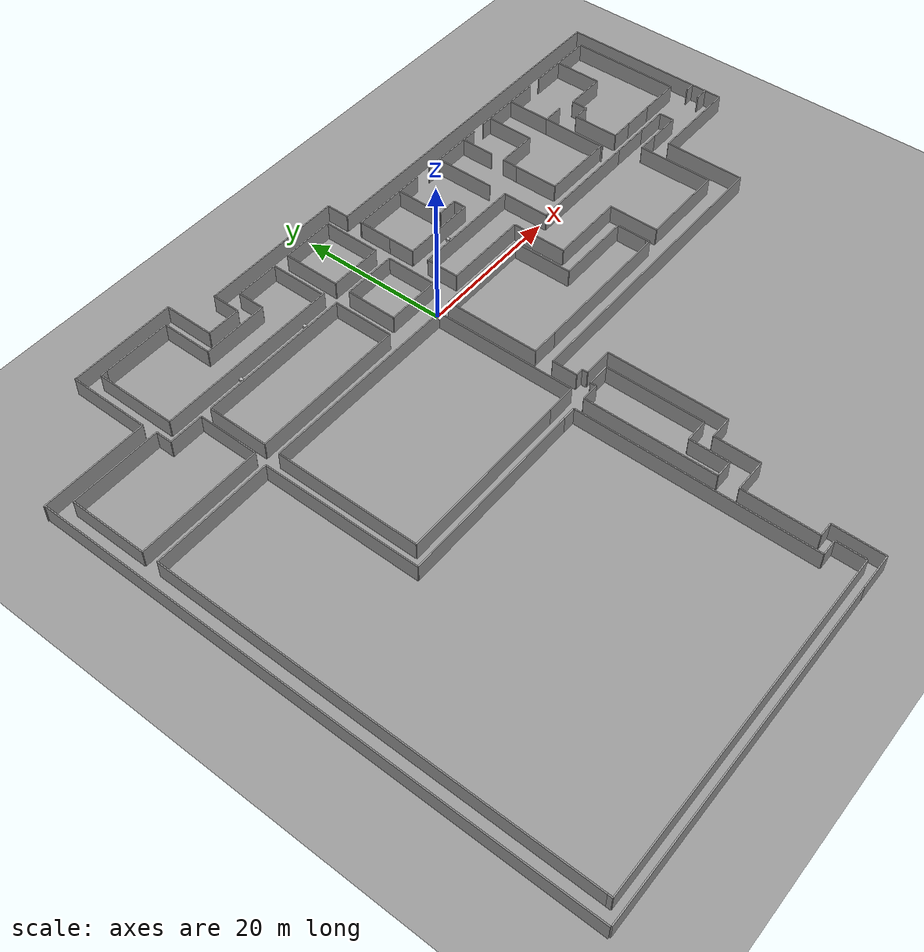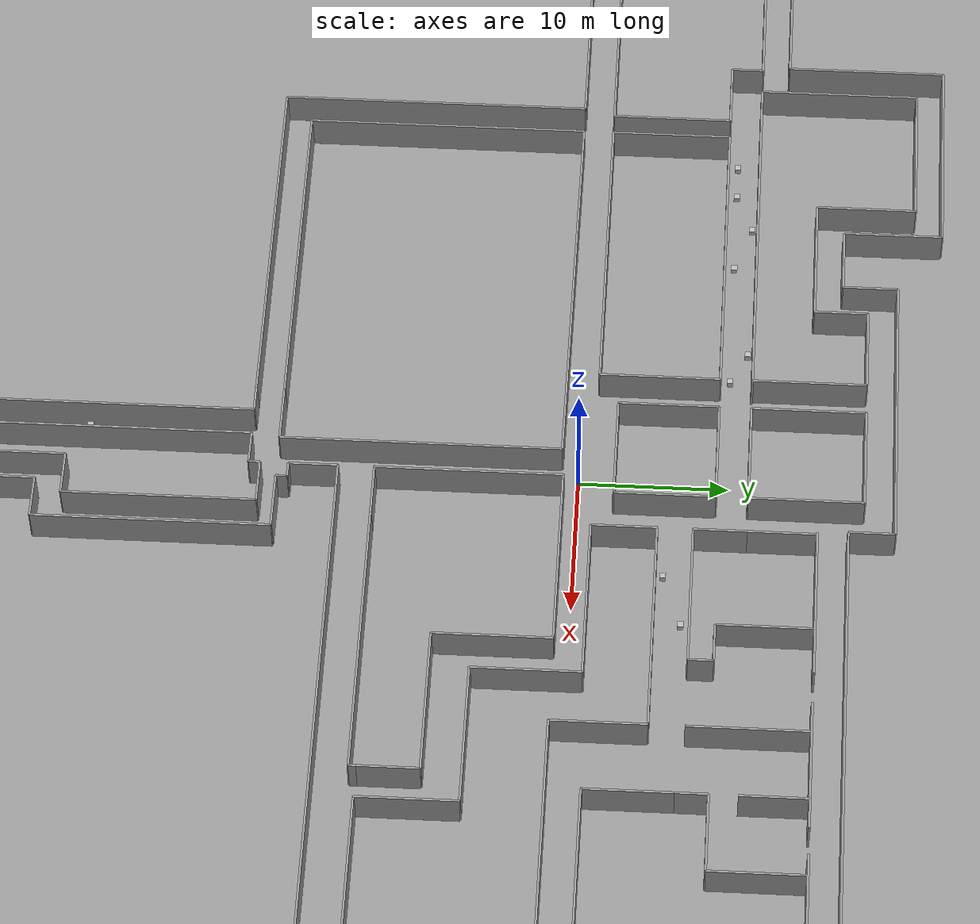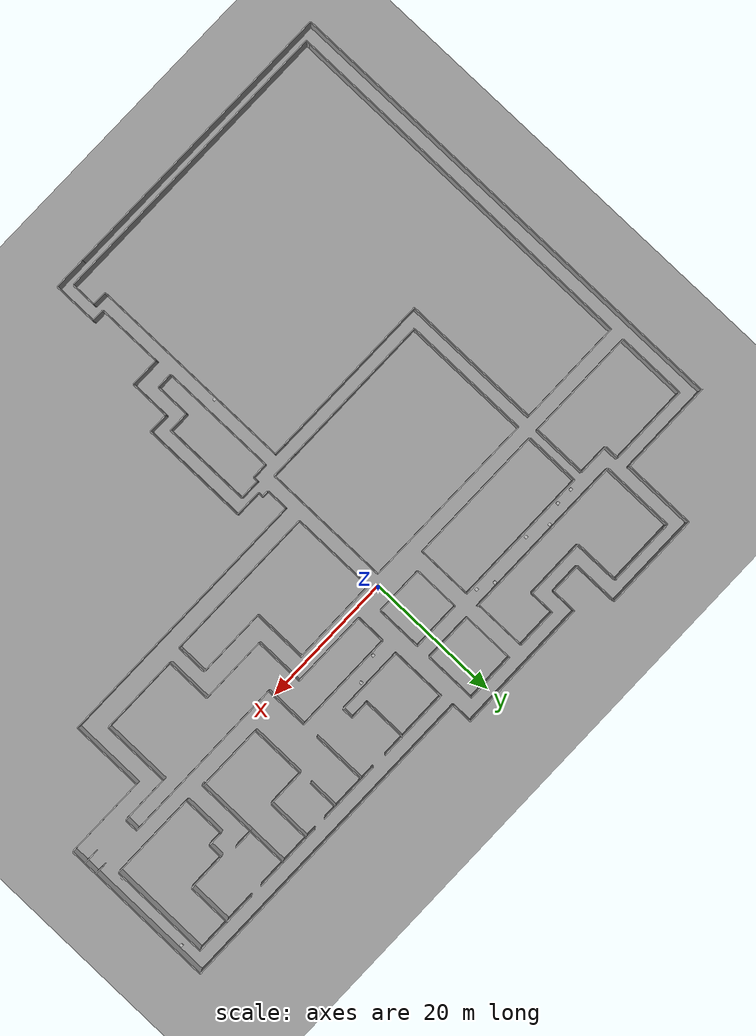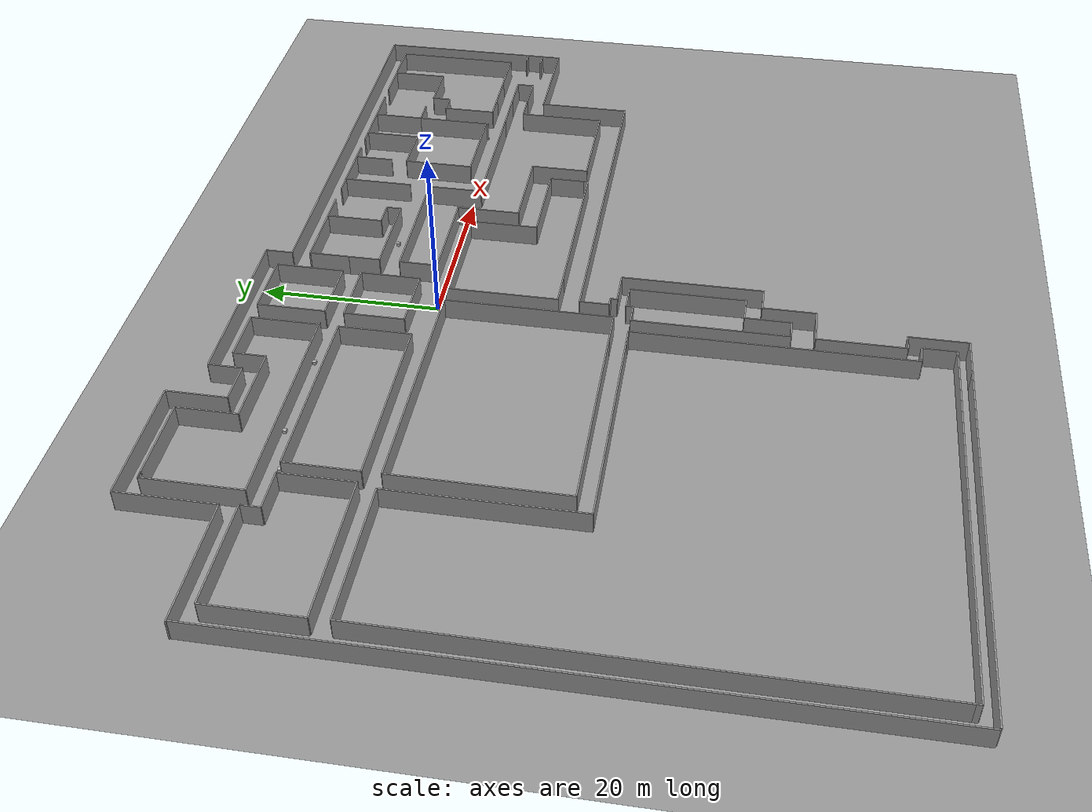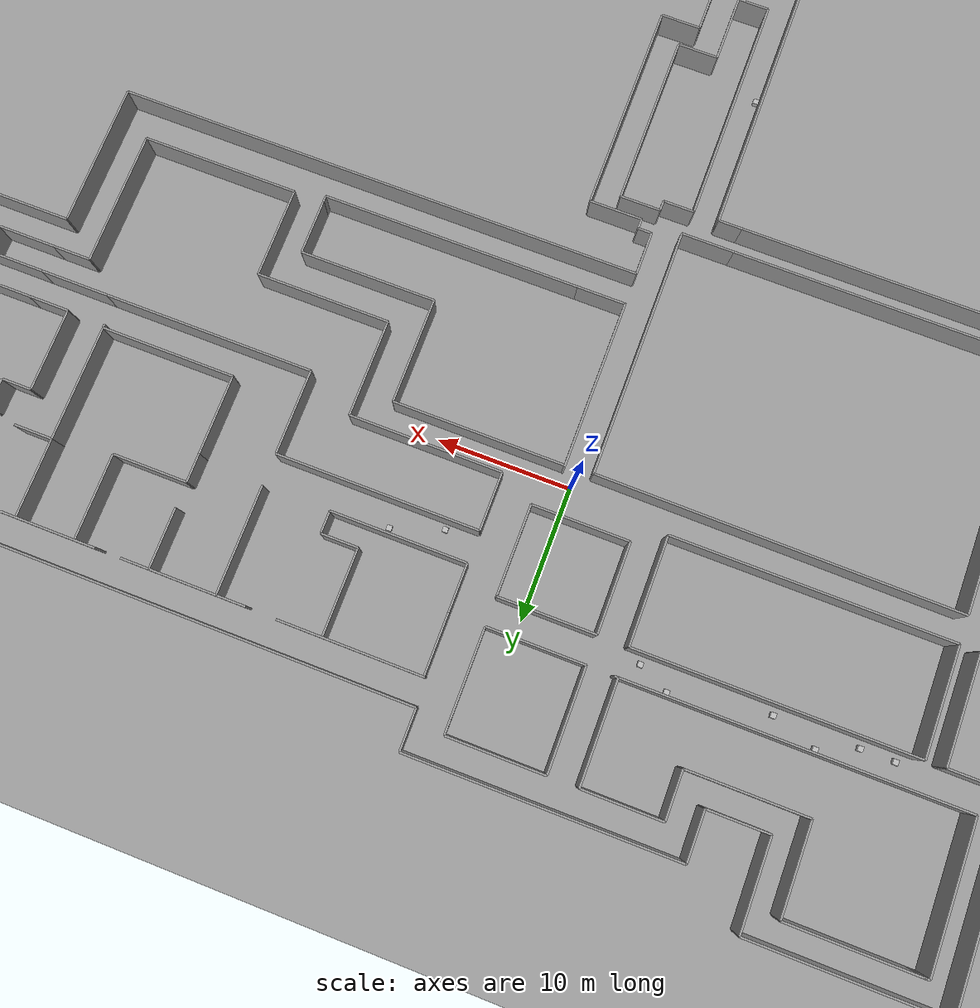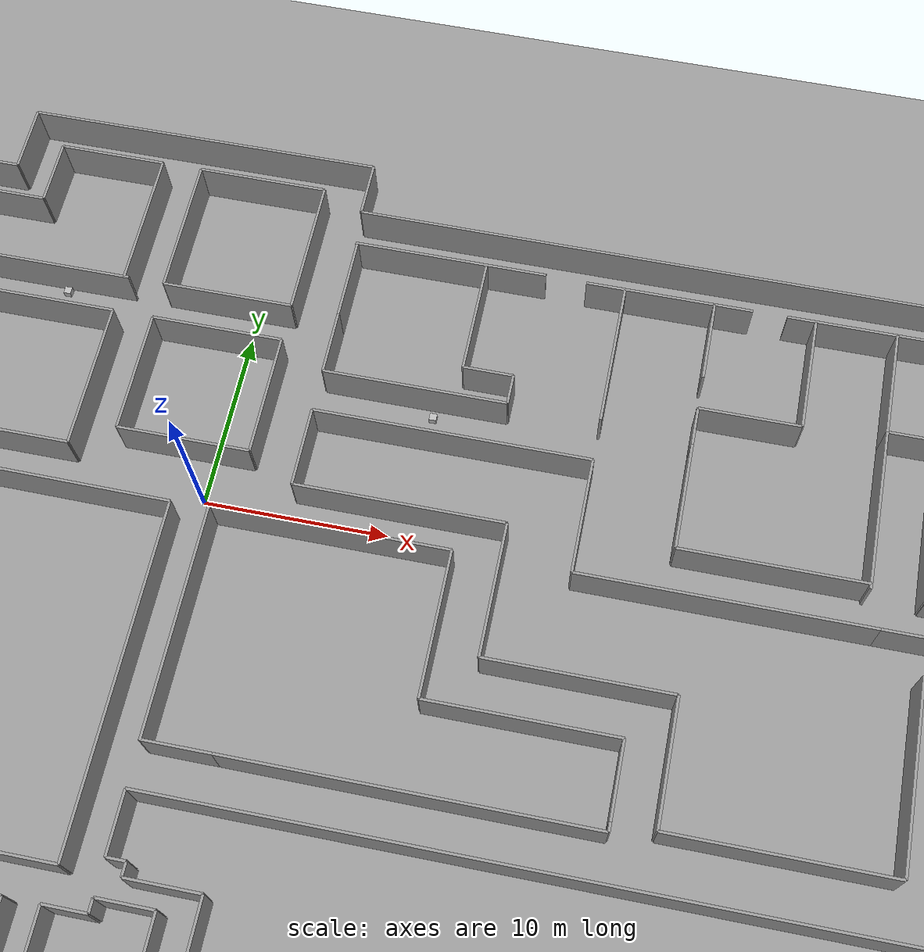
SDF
<sdf version="1.6">
 <world name="default">
  <scene><ambient>0 0 0 1</ambient><background>0.7 0.7 0.7 1</background><shadows>1</shadows></scene>
  <physics default="0" name="default_physics" type="ode">
   <max_step_size>0.005</max_step_size>
   <real_time_factor>1</real_time_factor>
   <real_time_update_rate>100</real_time_update_rate>
  </physics>
  <model name="ground_plane_0">
   <static>1</static>
   <link name="link">
    <collision name="collision">
     <geometry><plane><normal>0 0 1</normal><size>100 100</size></plane></geometry>
     <surface><friction><ode><mu>100</mu><mu2>50</mu2></ode></friction></surface>
    </collision>
    <visual name="visual">
     <cast_shadows>0</cast_shadows>
     <geometry><plane><normal>0 0 1</normal><size>100 100</size></plane></geometry>
     <material>
      <script><uri>file://media/materials/scripts/gazebo.material</uri><name>Gazebo/Grey</name></script>
     </material>
    </visual>
    <velocity_decay><linear>0</linear><angular>0</angular></velocity_decay>
   </link>
   <pose>0.497681 0 0 0 -0 0</pose>
  </model>
  <model name="Wean4Complete">
   <pose>-5 0 0 0 -0 0</pose>
   <static>1</static>
   <link name="Wall_0">
    <collision name="Wall_0_Collision">
     <geometry><box><size>2.162 0.15 2.5</size></box></geometry>
     <pose>0 0 1.25 0 -0 0</pose>
    </collision>
    <visual name="Wall_0_Visual">
     <pose>0 0 1.25 0 -0 0</pose>
     <geometry><box><size>2.162 0.15 2.5</size></box></geometry>
     <material>
      <script><uri>file://media/materials/scripts/gazebo.material</uri><name>Gazebo/Grey</name></script>
      <ambient>1 1 1 1</ambient>
     </material>
    </visual>
    <pose>-29.104 10.27 0 0 0 1.57079632679</pose>
   </link>
   <link name="Wall_1">
    <collision name="Wall_1_Collision">
     <geometry><box><size>8.108 0.15 2.5</size></box></geometry>
     <pose>0 0 1.25 0 -0 0</pose>
    </collision>
    <visual name="Wall_1_Visual">
     <pose>0 0 1.25 0 -0 0</pose>
     <geometry><box><size>8.108 0.15 2.5</size></box></geometry>
     <material>
      <script><uri>file://media/materials/scripts/gazebo.material</uri><name>Gazebo/Grey</name></script>
      <ambient>1 1 1 1</ambient>
     </material>
    </visual>
    <pose>-24.509 5.135 0 0 0 1.57079632679</pose>
   </link>
   <link name="Wall_2">
    <collision name="Wall_2_Collision">
     <geometry><box><size>16.541 0.15 2.5</size></box></geometry>
     <pose>0 0 1.25 0 -0 0</pose>
    </collision>
    <visual name="Wall_2_Visual">
     <pose>0 0 1.25 0 -0 0</pose>
     <geometry><box><size>16.541 0.15 2.5</size></box></geometry>
     <material>
      <script><uri>file://media/materials/scripts/gazebo.material</uri><name>Gazebo/Grey</name></script>
      <ambient>1 1 1 1</ambient>
     </material>
    </visual>
    <pose>-32.7795 1.081 0 0 0 0.0</pose>
   </link>
   <link name="Wall_3">
    <collision name="Wall_3_Collision">
     <geometry><box><size>4.595 0.15 2.5</size></box></geometry>
     <pose>0 0 1.25 0 -0 0</pose>
    </collision>
    <visual name="Wall_3_Visual">
     <pose>0 0 1.25 0 -0 0</pose>
     <geometry><box><size>4.595 0.15 2.5</size></box></geometry>
     <material>
      <script><uri>file://media/materials/scripts/gazebo.material</uri><name>Gazebo/Grey</name></script>
      <ambient>1 1 1 1</ambient>
     </material>
    </visual>
    <pose>-26.8065 9.189 0 0 0 0.0</pose>
   </link>
   <link name="Wall_4">
    <collision name="Wall_4_Collision">
     <geometry><box><size>8.108 0.15 2.5</size></box></geometry>
     <pose>0 0 1.25 0 -0 0</pose>
    </collision>
    <visual name="Wall_4_Visual">
     <pose>0 0 1.25 0 -0 0</pose>
     <geometry><box><size>8.108 0.15 2.5</size></box></geometry>
     <material>
      <script><uri>file://media/materials/scripts/gazebo.material</uri><name>Gazebo/Grey</name></script>
      <ambient>1 1 1 1</ambient>
     </material>
    </visual>
    <pose>-23.05 5.135 0 0 0 1.57079632679</pose>
   </link>
   <link name="Wall_5">
    <collision name="Wall_5_Collision">
     <geometry><box><size>20.703 0.15 2.5</size></box></geometry>
     <pose>0 0 1.25 0 -0 0</pose>
    </collision>
    <visual name="Wall_5_Visual">
     <pose>0 0 1.25 0 -0 0</pose>
     <geometry><box><size>20.703 0.15 2.5</size></box></geometry>
     <material>
      <script><uri>file://media/materials/scripts/gazebo.material</uri><name>Gazebo/Grey</name></script>
      <ambient>1 1 1 1</ambient>
     </material>
    </visual>
    <pose>-12.6985 1.081 0 0 0 0.0</pose>
   </link>
   <link name="Wall_6">
    <collision name="Wall_6_Collision">
     <geometry><box><size>8.108 0.15 2.5</size></box></geometry>
     <pose>0 0 1.25 0 -0 0</pose>
    </collision>
    <visual name="Wall_6_Visual">
     <pose>0 0 1.25 0 -0 0</pose>
     <geometry><box><size>8.108 0.15 2.5</size></box></geometry>
     <material>
      <script><uri>file://media/materials/scripts/gazebo.material</uri><name>Gazebo/Grey</name></script>
      <ambient>1 1 1 1</ambient>
     </material>
    </visual>
    <pose>-2.347 5.135 0 0 0 1.57079632679</pose>
   </link>
   <link name="Wall_7">
    <collision name="Wall_7_Collision">
     <geometry><box><size>20.703 0.15 2.5</size></box></geometry>
     <pose>0 0 1.25 0 -0 0</pose>
    </collision>
    <visual name="Wall_7_Visual">
     <pose>0 0 1.25 0 -0 0</pose>
     <geometry><box><size>20.703 0.15 2.5</size></box></geometry>
     <material>
      <script><uri>file://media/materials/scripts/gazebo.material</uri><name>Gazebo/Grey</name></script>
      <ambient>1 1 1 1</ambient>
     </material>
    </visual>
    <pose>-12.6985 9.189 0 0 0 0.0</pose>
   </link>
   <link name="Wall_8">
    <collision name="Wall_8_Collision">
     <geometry><box><size>25.135 0.15 2.5</size></box></geometry>
     <pose>0 0 1.25 0 -0 0</pose>
    </collision>
    <visual name="Wall_8_Visual">
     <pose>0 0 1.25 0 -0 0</pose>
     <geometry><box><size>25.135 0.15 2.5</size></box></geometry>
     <material>
      <script><uri>file://media/materials/scripts/gazebo.material</uri><name>Gazebo/Grey</name></script>
      <ambient>1 1 1 1</ambient>
     </material>
    </visual>
    <pose>-14.6445 11.351 0 0 0 0.0</pose>
   </link>
   <link name="Wall_9">
    <collision name="Wall_9_Collision">
     <geometry><box><size>7.676 0.15 2.5</size></box></geometry>
     <pose>0 0 1.25 0 -0 0</pose>
    </collision>
    <visual name="Wall_9_Visual">
     <pose>0 0 1.25 0 -0 0</pose>
     <geometry><box><size>7.676 0.15 2.5</size></box></geometry>
     <material>
      <script><uri>file://media/materials/scripts/gazebo.material</uri><name>Gazebo/Grey</name></script>
      <ambient>1 1 1 1</ambient>
     </material>
    </visual>
    <pose>-2.347 15.189 0 0 0 1.57079632679</pose>
   </link>
   <link name="Wall_10">
    <collision name="Wall_10_Collision">
     <geometry><box><size>5.946 0.15 2.5</size></box></geometry>
     <pose>0 0 1.25 0 -0 0</pose>
    </collision>
    <visual name="Wall_10_Visual">
     <pose>0 0 1.25 0 -0 0</pose>
     <geometry><box><size>5.946 0.15 2.5</size></box></geometry>
     <material>
      <script><uri>file://media/materials/scripts/gazebo.material</uri><name>Gazebo/Grey</name></script>
      <ambient>1 1 1 1</ambient>
     </material>
    </visual>
    <pose>-5.32 19.027 0 0 0 0.0</pose>
   </link>
   <link name="Wall_11">
    <collision name="Wall_11_Collision">
     <geometry><box><size>3.622 0.15 2.5</size></box></geometry>
     <pose>0 0 1.25 0 -0 0</pose>
    </collision>
    <visual name="Wall_11_Visual">
     <pose>0 0 1.25 0 -0 0</pose>
     <geometry><box><size>3.622 0.15 2.5</size></box></geometry>
     <material>
      <script><uri>file://media/materials/scripts/gazebo.material</uri><name>Gazebo/Grey</name></script>
      <ambient>1 1 1 1</ambient>
     </material>
    </visual>
    <pose>-8.293 17.216 0 0 0 1.57079632679</pose>
   </link>
   <link name="Wall_12">
    <collision name="Wall_12_Collision">
     <geometry><box><size>8.919 0.15 2.5</size></box></geometry>
     <pose>0 0 1.25 0 -0 0</pose>
    </collision>
    <visual name="Wall_12_Visual">
     <pose>0 0 1.25 0 -0 0</pose>
     <geometry><box><size>8.919 0.15 2.5</size></box></geometry>
     <material>
      <script><uri>file://media/materials/scripts/gazebo.material</uri><name>Gazebo/Grey</name></script>
      <ambient>1 1 1 1</ambient>
     </material>
    </visual>
    <pose>-12.7525 15.405 0 0 0 0.0</pose>
   </link>
   <link name="Wall_13">
    <collision name="Wall_13_Collision">
     <geometry><box><size>6.757 0.15 2.5</size></box></geometry>
     <pose>0 0 1.25 0 -0 0</pose>
    </collision>
    <visual name="Wall_13_Visual">
     <pose>0 0 1.25 0 -0 0</pose>
     <geometry><box><size>6.757 0.15 2.5</size></box></geometry>
     <material>
      <script><uri>file://media/materials/scripts/gazebo.material</uri><name>Gazebo/Grey</name></script>
      <ambient>1 1 1 1</ambient>
     </material>
    </visual>
    <pose>-17.212 18.7835 0 0 0 1.57079632679</pose>
   </link>
   <link name="Wall_14">
    <collision name="Wall_14_Collision">
     <geometry><box><size>9.838 0.15 2.5</size></box></geometry>
     <pose>0 0 1.25 0 -0 0</pose>
    </collision>
    <visual name="Wall_14_Visual">
     <pose>0 0 1.25 0 -0 0</pose>
     <geometry><box><size>9.838 0.15 2.5</size></box></geometry>
     <material>
      <script><uri>file://media/materials/scripts/gazebo.material</uri><name>Gazebo/Grey</name></script>
      <ambient>1 1 1 1</ambient>
     </material>
    </visual>
    <pose>-22.131 22.162 0 0 0 0.0</pose>
   </link>
   <link name="Wall_15">
    <collision name="Wall_15_Collision">
     <geometry><box><size>10.811 0.15 2.5</size></box></geometry>
     <pose>0 0 1.25 0 -0 0</pose>
    </collision>
    <visual name="Wall_15_Visual">
     <pose>0 0 1.25 0 -0 0</pose>
     <geometry><box><size>10.811 0.15 2.5</size></box></geometry>
     <material>
      <script><uri>file://media/materials/scripts/gazebo.material</uri><name>Gazebo/Grey</name></script>
      <ambient>1 1 1 1</ambient>
     </material>
    </visual>
    <pose>-27.212 16.7565 0 0 0 1.57079632679</pose>
   </link>
   <link name="Wall_16">
    <collision name="Wall_16_Collision">
     <geometry><box><size>0.811 0.15 2.5</size></box></geometry>
     <pose>0 0 1.25 0 -0 0</pose>
    </collision>
    <visual name="Wall_16_Visual">
     <pose>0 0 1.25 0 -0 0</pose>
     <geometry><box><size>0.811 0.15 2.5</size></box></geometry>
     <material>
      <script><uri>file://media/materials/scripts/gazebo.material</uri><name>Gazebo/Grey</name></script>
      <ambient>1 1 1 1</ambient>
     </material>
    </visual>
    <pose>-26.8065 22.162 0 0 0 0.0</pose>
   </link>
   <link name="Wall_17">
    <collision name="Wall_17_Collision">
     <geometry><box><size>11.946 0.15 2.5</size></box></geometry>
     <pose>0 0 1.25 0 -0 0</pose>
    </collision>
    <visual name="Wall_17_Visual">
     <pose>0 0 1.25 0 -0 0</pose>
     <geometry><box><size>11.946 0.15 2.5</size></box></geometry>
     <material>
      <script><uri>file://media/materials/scripts/gazebo.material</uri><name>Gazebo/Grey</name></script>
      <ambient>1 1 1 1</ambient>
     </material>
    </visual>
    <pose>-35.077 11.351 0 0 0 0.0</pose>
   </link>
   <link name="Wall_18">
    <collision name="Wall_18_Collision">
     <geometry><box><size>10.27 0.15 2.5</size></box></geometry>
     <pose>0 0 1.25 0 -0 0</pose>
    </collision>
    <visual name="Wall_18_Visual">
     <pose>0 0 1.25 0 -0 0</pose>
     <geometry><box><size>10.27 0.15 2.5</size></box></geometry>
     <material>
      <script><uri>file://media/materials/scripts/gazebo.material</uri><name>Gazebo/Grey</name></script>
      <ambient>1 1 1 1</ambient>
     </material>
    </visual>
    <pose>-41.05 6.216 0 0 0 1.57079632679</pose>
   </link>
   <link name="Wall_19">
    <collision name="Wall_19_Collision">
     <geometry><box><size>10.757 0.15 2.5</size></box></geometry>
     <pose>0 0 1.25 0 -0 0</pose>
    </collision>
    <visual name="Wall_19_Visual">
     <pose>0 0 1.25 0 -0 0</pose>
     <geometry><box><size>10.757 0.15 2.5</size></box></geometry>
     <material>
      <script><uri>file://media/materials/scripts/gazebo.material</uri><name>Gazebo/Grey</name></script>
      <ambient>1 1 1 1</ambient>
     </material>
    </visual>
    <pose>-29.374 18.6215 0 0 0 1.57079632679</pose>
   </link>
   <link name="Wall_20">
    <collision name="Wall_20_Collision">
     <geometry><box><size>14.324 0.15 2.5</size></box></geometry>
     <pose>0 0 1.25 0 -0 0</pose>
    </collision>
    <visual name="Wall_20_Visual">
     <pose>0 0 1.25 0 -0 0</pose>
     <geometry><box><size>14.324 0.15 2.5</size></box></geometry>
     <material>
      <script><uri>file://media/materials/scripts/gazebo.material</uri><name>Gazebo/Grey</name></script>
      <ambient>1 1 1 1</ambient>
     </material>
    </visual>
    <pose>-22.212 24.0 0 0 0 0.0</pose>
   </link>
   <link name="Wall_21">
    <collision name="Wall_21_Collision">
     <geometry><box><size>6.703 0.15 2.5</size></box></geometry>
     <pose>0 0 1.25 0 -0 0</pose>
    </collision>
    <visual name="Wall_21_Visual">
     <pose>0 0 1.25 0 -0 0</pose>
     <geometry><box><size>6.703 0.15 2.5</size></box></geometry>
     <material>
      <script><uri>file://media/materials/scripts/gazebo.material</uri><name>Gazebo/Grey</name></script>
      <ambient>1 1 1 1</ambient>
     </material>
    </visual>
    <pose>-15.05 20.6485 0 0 0 1.57079632679</pose>
   </link>
   <link name="Wall_22">
    <collision name="Wall_22_Collision">
     <geometry><box><size>4.595 0.15 2.5</size></box></geometry>
     <pose>0 0 1.25 0 -0 0</pose>
    </collision>
    <visual name="Wall_22_Visual">
     <pose>0 0 1.25 0 -0 0</pose>
     <geometry><box><size>4.595 0.15 2.5</size></box></geometry>
     <material>
      <script><uri>file://media/materials/scripts/gazebo.material</uri><name>Gazebo/Grey</name></script>
      <ambient>1 1 1 1</ambient>
     </material>
    </visual>
    <pose>-12.7525 17.297 0 0 0 0.0</pose>
   </link>
   <link name="Wall_23">
    <collision name="Wall_23_Collision">
     <geometry><box><size>3.73 0.15 2.5</size></box></geometry>
     <pose>0 0 1.25 0 -0 0</pose>
    </collision>
    <visual name="Wall_23_Visual">
     <pose>0 0 1.25 0 -0 0</pose>
     <geometry><box><size>3.73 0.15 2.5</size></box></geometry>
     <material>
      <script><uri>file://media/materials/scripts/gazebo.material</uri><name>Gazebo/Grey</name></script>
      <ambient>1 1 1 1</ambient>
     </material>
    </visual>
    <pose>-10.455 19.162 0 0 0 1.57079632679</pose>
   </link>
   <link name="Wall_24">
    <collision name="Wall_24_Collision">
     <geometry><box><size>20.0000728999 0.15 2.5</size></box></geometry>
     <pose>0 0 1.25 0 -0 0</pose>
    </collision>
    <visual name="Wall_24_Visual">
     <pose>0 0 1.25 0 -0 0</pose>
     <geometry><box><size>20.0000728999 0.15 2.5</size></box></geometry>
     <material>
      <script><uri>file://media/materials/scripts/gazebo.material</uri><name>Gazebo/Grey</name></script>
      <ambient>1 1 1 1</ambient>
     </material>
    </visual>
    <pose>-0.455 21.054 0 0 0 0.00269999343903</pose>
   </link>
   <link name="Wall_25">
    <collision name="Wall_25_Collision">
     <geometry><box><size>7.676 0.15 2.5</size></box></geometry>
     <pose>0 0 1.25 0 -0 0</pose>
    </collision>
    <visual name="Wall_25_Visual">
     <pose>0 0 1.25 0 -0 0</pose>
     <geometry><box><size>7.676 0.15 2.5</size></box></geometry>
     <material>
      <script><uri>file://media/materials/scripts/gazebo.material</uri><name>Gazebo/Grey</name></script>
      <ambient>1 1 1 1</ambient>
     </material>
    </visual>
    <pose>-0.077 15.189 0 0 0 1.57079632679</pose>
   </link>
   <link name="Wall_26">
    <collision name="Wall_26_Collision">
     <geometry><box><size>7.243 0.15 2.5</size></box></geometry>
     <pose>0 0 1.25 0 -0 0</pose>
    </collision>
    <visual name="Wall_26_Visual">
     <pose>0 0 1.25 0 -0 0</pose>
     <geometry><box><size>7.243 0.15 2.5</size></box></geometry>
     <material>
      <script><uri>file://media/materials/scripts/gazebo.material</uri><name>Gazebo/Grey</name></script>
      <ambient>1 1 1 1</ambient>
     </material>
    </visual>
    <pose>3.5445 11.351 0 0 0 0.0</pose>
   </link>
   <link name="Wall_27">
    <collision name="Wall_27_Collision">
     <geometry><box><size>7.676 0.15 2.5</size></box></geometry>
     <pose>0 0 1.25 0 -0 0</pose>
    </collision>
    <visual name="Wall_27_Visual">
     <pose>0 0 1.25 0 -0 0</pose>
     <geometry><box><size>7.676 0.15 2.5</size></box></geometry>
     <material>
      <script><uri>file://media/materials/scripts/gazebo.material</uri><name>Gazebo/Grey</name></script>
      <ambient>1 1 1 1</ambient>
     </material>
    </visual>
    <pose>7.166 15.189 0 0 0 1.57079632679</pose>
   </link>
   <link name="Wall_28">
    <collision name="Wall_28_Collision">
     <geometry><box><size>7.243 0.15 2.5</size></box></geometry>
     <pose>0 0 1.25 0 -0 0</pose>
    </collision>
    <visual name="Wall_28_Visual">
     <pose>0 0 1.25 0 -0 0</pose>
     <geometry><box><size>7.243 0.15 2.5</size></box></geometry>
     <material>
      <script><uri>file://media/materials/scripts/gazebo.material</uri><name>Gazebo/Grey</name></script>
      <ambient>1 1 1 1</ambient>
     </material>
    </visual>
    <pose>3.5445 19.027 0 0 0 0.0</pose>
   </link>
   <link name="Wall_29">
    <collision name="Wall_29_Collision">
     <geometry><box><size>3.081 0.15 2.5</size></box></geometry>
     <pose>0 0 1.25 0 -0 0</pose>
    </collision>
    <visual name="Wall_29_Visual">
     <pose>0 0 1.25 0 -0 0</pose>
     <geometry><box><size>3.081 0.15 2.5</size></box></geometry>
     <material>
      <script><uri>file://media/materials/scripts/gazebo.material</uri><name>Gazebo/Grey</name></script>
      <ambient>1 1 1 1</ambient>
     </material>
    </visual>
    <pose>9.545 19.5405 0 0 0 1.57079632679</pose>
   </link>
   <link name="Wall_30">
    <collision name="Wall_30_Collision">
     <geometry><box><size>48.378 0.15 2.5</size></box></geometry>
     <pose>0 0 1.25 0 -0 0</pose>
    </collision>
    <visual name="Wall_30_Visual">
     <pose>0 0 1.25 0 -0 0</pose>
     <geometry><box><size>48.378 0.15 2.5</size></box></geometry>
     <material>
      <script><uri>file://media/materials/scripts/gazebo.material</uri><name>Gazebo/Grey</name></script>
      <ambient>1 1 1 1</ambient>
     </material>
    </visual>
    <pose>33.734 18.0 0 0 0 0.0</pose>
   </link>
   <link name="Wall_31">
    <collision name="Wall_31_Collision">
     <geometry><box><size>23.189 0.15 2.5</size></box></geometry>
     <pose>0 0 1.25 0 -0 0</pose>
    </collision>
    <visual name="Wall_31_Visual">
     <pose>0 0 1.25 0 -0 0</pose>
     <geometry><box><size>23.189 0.15 2.5</size></box></geometry>
     <material>
      <script><uri>file://media/materials/scripts/gazebo.material</uri><name>Gazebo/Grey</name></script>
      <ambient>1 1 1 1</ambient>
     </material>
    </visual>
    <pose>57.923 6.4055 0 0 0 1.57079632679</pose>
   </link>
   <link name="Wall_32">
    <collision name="Wall_32_Collision">
     <geometry><box><size>1.838 0.15 2.5</size></box></geometry>
     <pose>0 0 1.25 0 -0 0</pose>
    </collision>
    <visual name="Wall_32_Visual">
     <pose>0 0 1.25 0 -0 0</pose>
     <geometry><box><size>1.838 0.15 2.5</size></box></geometry>
     <material>
      <script><uri>file://media/materials/scripts/gazebo.material</uri><name>Gazebo/Grey</name></script>
      <ambient>1 1 1 1</ambient>
     </material>
    </visual>
    <pose>57.004 -2.973 0 0 0 0.0</pose>
   </link>
   <link name="Wall_33">
    <collision name="Wall_33_Collision">
     <geometry><box><size>1.351 0.15 2.5</size></box></geometry>
     <pose>0 0 1.25 0 -0 0</pose>
    </collision>
    <visual name="Wall_33_Visual">
     <pose>0 0 1.25 0 -0 0</pose>
     <geometry><box><size>1.351 0.15 2.5</size></box></geometry>
     <material>
      <script><uri>file://media/materials/scripts/gazebo.material</uri><name>Gazebo/Grey</name></script>
      <ambient>1 1 1 1</ambient>
     </material>
    </visual>
    <pose>57.2475 -0.973 0 0 0 0.0</pose>
   </link>
   <link name="Wall_34">
    <collision name="Wall_34_Collision">
     <geometry><box><size>12.162 0.15 2.5</size></box></geometry>
     <pose>0 0 1.25 0 -0 0</pose>
    </collision>
    <visual name="Wall_34_Visual">
     <pose>0 0 1.25 0 -0 0</pose>
     <geometry><box><size>12.162 0.15 2.5</size></box></geometry>
     <material>
      <script><uri>file://media/materials/scripts/gazebo.material</uri><name>Gazebo/Grey</name></script>
      <ambient>1 1 1 1</ambient>
     </material>
    </visual>
    <pose>51.842 -5.189 0 0 0 0.0</pose>
   </link>
   <link name="Wall_35">
    <collision name="Wall_35_Collision">
     <geometry><box><size>4.378 0.15 2.5</size></box></geometry>
     <pose>0 0 1.25 0 -0 0</pose>
    </collision>
    <visual name="Wall_35_Visual">
     <pose>0 0 1.25 0 -0 0</pose>
     <geometry><box><size>4.378 0.15 2.5</size></box></geometry>
     <material>
      <script><uri>file://media/materials/scripts/gazebo.material</uri><name>Gazebo/Grey</name></script>
      <ambient>1 1 1 1</ambient>
     </material>
    </visual>
    <pose>47.95 -2.973 0 0 0 0.0</pose>
   </link>
   <link name="Wall_36">
    <collision name="Wall_36_Collision">
     <geometry><box><size>2.0 0.15 2.5</size></box></geometry>
     <pose>0 0 1.25 0 -0 0</pose>
    </collision>
    <visual name="Wall_36_Visual">
     <pose>0 0 1.25 0 -0 0</pose>
     <geometry><box><size>2.0 0.15 2.5</size></box></geometry>
     <material>
      <script><uri>file://media/materials/scripts/gazebo.material</uri><name>Gazebo/Grey</name></script>
      <ambient>1 1 1 1</ambient>
     </material>
    </visual>
    <pose>50.139 -1.973 0 0 0 1.57079632679</pose>
   </link>
   <link name="Wall_37">
    <collision name="Wall_37_Collision">
     <geometry><box><size>4.378 0.15 2.5</size></box></geometry>
     <pose>0 0 1.25 0 -0 0</pose>
    </collision>
    <visual name="Wall_37_Visual">
     <pose>0 0 1.25 0 -0 0</pose>
     <geometry><box><size>4.378 0.15 2.5</size></box></geometry>
     <material>
      <script><uri>file://media/materials/scripts/gazebo.material</uri><name>Gazebo/Grey</name></script>
      <ambient>1 1 1 1</ambient>
     </material>
    </visual>
    <pose>47.95 -0.973 0 0 0 0.0</pose>
   </link>
   <link name="Wall_38">
    <collision name="Wall_38_Collision">
     <geometry><box><size>4.378 0.15 2.5</size></box></geometry>
     <pose>0 0 1.25 0 -0 0</pose>
    </collision>
    <visual name="Wall_38_Visual">
     <pose>0 0 1.25 0 -0 0</pose>
     <geometry><box><size>4.378 0.15 2.5</size></box></geometry>
     <material>
      <script><uri>file://media/materials/scripts/gazebo.material</uri><name>Gazebo/Grey</name></script>
      <ambient>1 1 1 1</ambient>
     </material>
    </visual>
    <pose>47.95 1.081 0 0 0 0.0</pose>
   </link>
   <link name="Wall_39">
    <collision name="Wall_39_Collision">
     <geometry><box><size>5.622 0.15 2.5</size></box></geometry>
     <pose>0 0 1.25 0 -0 0</pose>
    </collision>
    <visual name="Wall_39_Visual">
     <pose>0 0 1.25 0 -0 0</pose>
     <geometry><box><size>5.622 0.15 2.5</size></box></geometry>
     <material>
      <script><uri>file://media/materials/scripts/gazebo.material</uri><name>Gazebo/Grey</name></script>
      <ambient>1 1 1 1</ambient>
     </material>
    </visual>
    <pose>52.95 1.081 0 0 0 0.0</pose>
   </link>
   <link name="Wall_40">
    <collision name="Wall_40_Collision">
     <geometry><box><size>14.811 0.15 2.5</size></box></geometry>
     <pose>0 0 1.25 0 -0 0</pose>
    </collision>
    <visual name="Wall_40_Visual">
     <pose>0 0 1.25 0 -0 0</pose>
     <geometry><box><size>14.811 0.15 2.5</size></box></geometry>
     <material>
      <script><uri>file://media/materials/scripts/gazebo.material</uri><name>Gazebo/Grey</name></script>
      <ambient>1 1 1 1</ambient>
     </material>
    </visual>
    <pose>55.761 8.4865 0 0 0 1.57079632679</pose>
   </link>
   <link name="Wall_41">
    <collision name="Wall_41_Collision">
     <geometry><box><size>9.676 0.15 2.5</size></box></geometry>
     <pose>0 0 1.25 0 -0 0</pose>
    </collision>
    <visual name="Wall_41_Visual">
     <pose>0 0 1.25 0 -0 0</pose>
     <geometry><box><size>9.676 0.15 2.5</size></box></geometry>
     <material>
      <script><uri>file://media/materials/scripts/gazebo.material</uri><name>Gazebo/Grey</name></script>
      <ambient>1 1 1 1</ambient>
     </material>
    </visual>
    <pose>50.923 15.892 0 0 0 0.0</pose>
   </link>
   <link name="Wall_42">
    <collision name="Wall_42_Collision">
     <geometry><box><size>10.27 0.15 2.5</size></box></geometry>
     <pose>0 0 1.25 0 -0 0</pose>
    </collision>
    <visual name="Wall_42_Visual">
     <pose>0 0 1.25 0 -0 0</pose>
     <geometry><box><size>10.27 0.15 2.5</size></box></geometry>
     <material>
      <script><uri>file://media/materials/scripts/gazebo.material</uri><name>Gazebo/Grey</name></script>
      <ambient>1 1 1 1</ambient>
     </material>
    </visual>
    <pose>39.058 15.892 0 0 0 0.0</pose>
   </link>
   <link name="Wall_43">
    <collision name="Wall_43_Collision">
     <geometry><box><size>9.243 0.15 2.5</size></box></geometry>
     <pose>0 0 1.25 0 -0 0</pose>
    </collision>
    <visual name="Wall_43_Visual">
     <pose>0 0 1.25 0 -0 0</pose>
     <geometry><box><size>9.243 0.15 2.5</size></box></geometry>
     <material>
      <script><uri>file://media/materials/scripts/gazebo.material</uri><name>Gazebo/Grey</name></script>
      <ambient>1 1 1 1</ambient>
     </material>
    </visual>
    <pose>27.4095 15.892 0 0 0 0.0</pose>
   </link>
   <link name="Wall_44">
    <collision name="Wall_44_Collision">
     <geometry><box><size>6.433 0.15 2.5</size></box></geometry>
     <pose>0 0 1.25 0 -0 0</pose>
    </collision>
    <visual name="Wall_44_Visual">
     <pose>0 0 1.25 0 -0 0</pose>
     <geometry><box><size>6.433 0.15 2.5</size></box></geometry>
     <material>
      <script><uri>file://media/materials/scripts/gazebo.material</uri><name>Gazebo/Grey</name></script>
      <ambient>1 1 1 1</ambient>
     </material>
    </visual>
    <pose>50.626 12.6755 0 0 0 1.57079632679</pose>
   </link>
   <link name="Wall_45">
    <collision name="Wall_45_Collision">
     <geometry><box><size>5.622 0.15 2.5</size></box></geometry>
     <pose>0 0 1.25 0 -0 0</pose>
    </collision>
    <visual name="Wall_45_Visual">
     <pose>0 0 1.25 0 -0 0</pose>
     <geometry><box><size>5.622 0.15 2.5</size></box></geometry>
     <material>
      <script><uri>file://media/materials/scripts/gazebo.material</uri><name>Gazebo/Grey</name></script>
      <ambient>1 1 1 1</ambient>
     </material>
    </visual>
    <pose>47.815 9.459 0 0 0 0.0</pose>
   </link>
   <link name="Wall_46">
    <collision name="Wall_46_Collision">
     <geometry><box><size>2.162 0.15 2.5</size></box></geometry>
     <pose>0 0 1.25 0 -0 0</pose>
    </collision>
    <visual name="Wall_46_Visual">
     <pose>0 0 1.25 0 -0 0</pose>
     <geometry><box><size>2.162 0.15 2.5</size></box></geometry>
     <material>
      <script><uri>file://media/materials/scripts/gazebo.material</uri><name>Gazebo/Grey</name></script>
      <ambient>1 1 1 1</ambient>
     </material>
    </visual>
    <pose>45.004 8.378 0 0 0 1.57079632679</pose>
   </link>
   <link name="Wall_47">
    <collision name="Wall_47_Collision">
     <geometry><box><size>2.162 0.15 2.5</size></box></geometry>
     <pose>0 0 1.25 0 -0 0</pose>
    </collision>
    <visual name="Wall_47_Visual">
     <pose>0 0 1.25 0 -0 0</pose>
     <geometry><box><size>2.162 0.15 2.5</size></box></geometry>
     <material>
      <script><uri>file://media/materials/scripts/gazebo.material</uri><name>Gazebo/Grey</name></script>
      <ambient>1 1 1 1</ambient>
     </material>
    </visual>
    <pose>43.869 7.297 0 0 0 0.0</pose>
   </link>
   <link name="Wall_48">
    <collision name="Wall_48_Collision">
     <geometry><box><size>6.216 0.15 2.5</size></box></geometry>
     <pose>0 0 1.25 0 -0 0</pose>
    </collision>
    <visual name="Wall_48_Visual">
     <pose>0 0 1.25 0 -0 0</pose>
     <geometry><box><size>6.216 0.15 2.5</size></box></geometry>
     <material>
      <script><uri>file://media/materials/scripts/gazebo.material</uri><name>Gazebo/Grey</name></script>
      <ambient>1 1 1 1</ambient>
     </material>
    </visual>
    <pose>42.788 4.189 0 0 0 1.57079632679</pose>
   </link>
   <link name="Wall_49">
    <collision name="Wall_49_Collision">
     <geometry><box><size>2.973 0.15 2.5</size></box></geometry>
     <pose>0 0 1.25 0 -0 0</pose>
    </collision>
    <visual name="Wall_49_Visual">
     <pose>0 0 1.25 0 -0 0</pose>
     <geometry><box><size>2.973 0.15 2.5</size></box></geometry>
     <material>
      <script><uri>file://media/materials/scripts/gazebo.material</uri><name>Gazebo/Grey</name></script>
      <ambient>1 1 1 1</ambient>
     </material>
    </visual>
    <pose>44.2745 1.081 0 0 0 0.0</pose>
   </link>
   <link name="Wall_50">
    <collision name="Wall_50_Collision">
     <geometry><box><size>5.135 0.15 2.5</size></box></geometry>
     <pose>0 0 1.25 0 -0 0</pose>
    </collision>
    <visual name="Wall_50_Visual">
     <pose>0 0 1.25 0 -0 0</pose>
     <geometry><box><size>5.135 0.15 2.5</size></box></geometry>
     <material>
      <script><uri>file://media/materials/scripts/gazebo.material</uri><name>Gazebo/Grey</name></script>
      <ambient>1 1 1 1</ambient>
     </material>
    </visual>
    <pose>43.1935 -0.973 0 0 0 0.0</pose>
   </link>
   <link name="Wall_51">
    <collision name="Wall_51_Collision">
     <geometry><box><size>8.919 0.15 2.5</size></box></geometry>
     <pose>0 0 1.25 0 -0 0</pose>
    </collision>
    <visual name="Wall_51_Visual">
     <pose>0 0 1.25 0 -0 0</pose>
     <geometry><box><size>8.919 0.15 2.5</size></box></geometry>
     <material>
      <script><uri>file://media/materials/scripts/gazebo.material</uri><name>Gazebo/Grey</name></script>
      <ambient>1 1 1 1</ambient>
     </material>
    </visual>
    <pose>39.923 5.5405 0 0 0 1.57079632679</pose>
   </link>
   <link name="Wall_52">
    <collision name="Wall_52_Collision">
     <geometry><box><size>2.865 0.15 2.5</size></box></geometry>
     <pose>0 0 1.25 0 -0 0</pose>
    </collision>
    <visual name="Wall_52_Visual">
     <pose>0 0 1.25 0 -0 0</pose>
     <geometry><box><size>2.865 0.15 2.5</size></box></geometry>
     <material>
      <script><uri>file://media/materials/scripts/gazebo.material</uri><name>Gazebo/Grey</name></script>
      <ambient>1 1 1 1</ambient>
     </material>
    </visual>
    <pose>41.3555 10.0 0 0 0 0.0</pose>
   </link>
   <link name="Wall_53">
    <collision name="Wall_53_Collision">
     <geometry><box><size>5.892 0.15 2.5</size></box></geometry>
     <pose>0 0 1.25 0 -0 0</pose>
    </collision>
    <visual name="Wall_53_Visual">
     <pose>0 0 1.25 0 -0 0</pose>
     <geometry><box><size>5.892 0.15 2.5</size></box></geometry>
     <material>
      <script><uri>file://media/materials/scripts/gazebo.material</uri><name>Gazebo/Grey</name></script>
      <ambient>1 1 1 1</ambient>
     </material>
    </visual>
    <pose>39.923 12.946 0 0 0 1.57079632679</pose>
   </link>
   <link name="Wall_54">
    <collision name="Wall_54_Collision">
     <geometry><box><size>10.757 0.15 2.5</size></box></geometry>
     <pose>0 0 1.25 0 -0 0</pose>
    </collision>
    <visual name="Wall_54_Visual">
     <pose>0 0 1.25 0 -0 0</pose>
     <geometry><box><size>10.757 0.15 2.5</size></box></geometry>
     <material>
      <script><uri>file://media/materials/scripts/gazebo.material</uri><name>Gazebo/Grey</name></script>
      <ambient>1 1 1 1</ambient>
     </material>
    </visual>
    <pose>45.761 -10.5675 0 0 0 1.57079632679</pose>
   </link>
   <link name="Wall_55">
    <collision name="Wall_55_Collision">
     <geometry><box><size>39.838 0.15 2.5</size></box></geometry>
     <pose>0 0 1.25 0 -0 0</pose>
    </collision>
    <visual name="Wall_55_Visual">
     <pose>0 0 1.25 0 -0 0</pose>
     <geometry><box><size>39.838 0.15 2.5</size></box></geometry>
     <material>
      <script><uri>file://media/materials/scripts/gazebo.material</uri><name>Gazebo/Grey</name></script>
      <ambient>1 1 1 1</ambient>
     </material>
    </visual>
    <pose>25.842 -15.946 0 0 0 0.0</pose>
   </link>
   <link name="Wall_56">
    <collision name="Wall_56_Collision">
     <geometry><box><size>4.541 0.15 2.5</size></box></geometry>
     <pose>0 0 1.25 0 -0 0</pose>
    </collision>
    <visual name="Wall_56_Visual">
     <pose>0 0 1.25 0 -0 0</pose>
     <geometry><box><size>4.541 0.15 2.5</size></box></geometry>
     <material>
      <script><uri>file://media/materials/scripts/gazebo.material</uri><name>Gazebo/Grey</name></script>
      <ambient>1 1 1 1</ambient>
     </material>
    </visual>
    <pose>9.815 13.6215 0 0 0 1.57079632679</pose>
   </link>
   <link name="Wall_57">
    <collision name="Wall_57_Collision">
     <geometry><box><size>4.541 0.15 2.5</size></box></geometry>
     <pose>0 0 1.25 0 -0 0</pose>
    </collision>
    <visual name="Wall_57_Visual">
     <pose>0 0 1.25 0 -0 0</pose>
     <geometry><box><size>4.541 0.15 2.5</size></box></geometry>
     <material>
      <script><uri>file://media/materials/scripts/gazebo.material</uri><name>Gazebo/Grey</name></script>
      <ambient>1 1 1 1</ambient>
     </material>
    </visual>
    <pose>29.923 13.6215 0 0 0 1.57079632679</pose>
   </link>
   <link name="Wall_58">
    <collision name="Wall_58_Collision">
     <geometry><box><size>6.433 0.15 2.5</size></box></geometry>
     <pose>0 0 1.25 0 -0 0</pose>
    </collision>
    <visual name="Wall_58_Visual">
     <pose>0 0 1.25 0 -0 0</pose>
     <geometry><box><size>6.433 0.15 2.5</size></box></geometry>
     <material>
      <script><uri>file://media/materials/scripts/gazebo.material</uri><name>Gazebo/Grey</name></script>
      <ambient>1 1 1 1</ambient>
     </material>
    </visual>
    <pose>35.491 12.6755 0 0 0 1.57079632679</pose>
   </link>
   <link name="Wall_59">
    <collision name="Wall_59_Collision">
     <geometry><box><size>5.568 0.15 2.5</size></box></geometry>
     <pose>0 0 1.25 0 -0 0</pose>
    </collision>
    <visual name="Wall_59_Visual">
     <pose>0 0 1.25 0 -0 0</pose>
     <geometry><box><size>5.568 0.15 2.5</size></box></geometry>
     <material>
      <script><uri>file://media/materials/scripts/gazebo.material</uri><name>Gazebo/Grey</name></script>
      <ambient>1 1 1 1</ambient>
     </material>
    </visual>
    <pose>32.707 9.459 0 0 0 0.0</pose>
   </link>
   <link name="Wall_60">
    <collision name="Wall_60_Collision">
     <geometry><box><size>2.162 0.15 2.5</size></box></geometry>
     <pose>0 0 1.25 0 -0 0</pose>
    </collision>
    <visual name="Wall_60_Visual">
     <pose>0 0 1.25 0 -0 0</pose>
     <geometry><box><size>2.162 0.15 2.5</size></box></geometry>
     <material>
      <script><uri>file://media/materials/scripts/gazebo.material</uri><name>Gazebo/Grey</name></script>
      <ambient>1 1 1 1</ambient>
     </material>
    </visual>
    <pose>29.923 8.378 0 0 0 1.57079632679</pose>
   </link>
   <link name="Wall_61">
    <collision name="Wall_61_Collision">
     <geometry><box><size>8.108 0.15 2.5</size></box></geometry>
     <pose>0 0 1.25 0 -0 0</pose>
    </collision>
    <visual name="Wall_61_Visual">
     <pose>0 0 1.25 0 -0 0</pose>
     <geometry><box><size>8.108 0.15 2.5</size></box></geometry>
     <material>
      <script><uri>file://media/materials/scripts/gazebo.material</uri><name>Gazebo/Grey</name></script>
      <ambient>1 1 1 1</ambient>
     </material>
    </visual>
    <pose>24.95 11.838 0 0 0 1.57079632679</pose>
   </link>
   <link name="Wall_62">
    <collision name="Wall_62_Collision">
     <geometry><box><size>6.433 0.15 2.5</size></box></geometry>
     <pose>0 0 1.25 0 -0 0</pose>
    </collision>
    <visual name="Wall_62_Visual">
     <pose>0 0 1.25 0 -0 0</pose>
     <geometry><box><size>6.433 0.15 2.5</size></box></geometry>
     <material>
      <script><uri>file://media/materials/scripts/gazebo.material</uri><name>Gazebo/Grey</name></script>
      <ambient>1 1 1 1</ambient>
     </material>
    </visual>
    <pose>17.166 12.6755 0 0 0 1.57079632679</pose>
   </link>
   <link name="Wall_63">
    <collision name="Wall_63_Collision">
     <geometry><box><size>2.757 0.15 2.5</size></box></geometry>
     <pose>0 0 1.25 0 -0 0</pose>
    </collision>
    <visual name="Wall_63_Visual">
     <pose>0 0 1.25 0 -0 0</pose>
     <geometry><box><size>2.757 0.15 2.5</size></box></geometry>
     <material>
      <script><uri>file://media/materials/scripts/gazebo.material</uri><name>Gazebo/Grey</name></script>
      <ambient>1 1 1 1</ambient>
     </material>
    </visual>
    <pose>18.5445 9.459 0 0 0 0.0</pose>
   </link>
   <link name="Wall_64">
    <collision name="Wall_64_Collision">
     <geometry><box><size>1.675 0.15 2.5</size></box></geometry>
     <pose>0 0 1.25 0 -0 0</pose>
    </collision>
    <visual name="Wall_64_Visual">
     <pose>0 0 1.25 0 -0 0</pose>
     <geometry><box><size>1.675 0.15 2.5</size></box></geometry>
     <material>
      <script><uri>file://media/materials/scripts/gazebo.material</uri><name>Gazebo/Grey</name></script>
      <ambient>1 1 1 1</ambient>
     </material>
    </visual>
    <pose>19.923 8.6215 0 0 0 1.57079632679</pose>
   </link>
   <link name="Wall_65">
    <collision name="Wall_65_Collision">
     <geometry><box><size>10.108 0.15 2.5</size></box></geometry>
     <pose>0 0 1.25 0 -0 0</pose>
    </collision>
    <visual name="Wall_65_Visual">
     <pose>0 0 1.25 0 -0 0</pose>
     <geometry><box><size>10.108 0.15 2.5</size></box></geometry>
     <material>
      <script><uri>file://media/materials/scripts/gazebo.material</uri><name>Gazebo/Grey</name></script>
      <ambient>1 1 1 1</ambient>
     </material>
    </visual>
    <pose>14.869 7.784 0 0 0 0.0</pose>
   </link>
   <link name="Wall_66">
    <collision name="Wall_66_Collision">
     <geometry><box><size>3.567 0.15 2.5</size></box></geometry>
     <pose>0 0 1.25 0 -0 0</pose>
    </collision>
    <visual name="Wall_66_Visual">
     <pose>0 0 1.25 0 -0 0</pose>
     <geometry><box><size>3.567 0.15 2.5</size></box></geometry>
     <material>
      <script><uri>file://media/materials/scripts/gazebo.material</uri><name>Gazebo/Grey</name></script>
      <ambient>1 1 1 1</ambient>
     </material>
    </visual>
    <pose>9.815 9.5675 0 0 0 1.57079632679</pose>
   </link>
   <link name="Wall_67">
    <collision name="Wall_67_Collision">
     <geometry><box><size>5.946 0.15 2.5</size></box></geometry>
     <pose>0 0 1.25 0 -0 0</pose>
    </collision>
    <visual name="Wall_67_Visual">
     <pose>0 0 1.25 0 -0 0</pose>
     <geometry><box><size>5.946 0.15 2.5</size></box></geometry>
     <material>
      <script><uri>file://media/materials/scripts/gazebo.material</uri><name>Gazebo/Grey</name></script>
      <ambient>1 1 1 1</ambient>
     </material>
    </visual>
    <pose>29.923 4.324 0 0 0 1.57079632679</pose>
   </link>
   <link name="Wall_68">
    <collision name="Wall_68_Collision">
     <geometry><box><size>10.0 0.15 2.5</size></box></geometry>
     <pose>0 0 1.25 0 -0 0</pose>
    </collision>
    <visual name="Wall_68_Visual">
     <pose>0 0 1.25 0 -0 0</pose>
     <geometry><box><size>10.0 0.15 2.5</size></box></geometry>
     <material>
      <script><uri>file://media/materials/scripts/gazebo.material</uri><name>Gazebo/Grey</name></script>
      <ambient>1 1 1 1</ambient>
     </material>
    </visual>
    <pose>34.923 1.351 0 0 0 0.0</pose>
   </link>
   <link name="Wall_69">
    <collision name="Wall_69_Collision">
     <geometry><box><size>15.135 0.15 2.5</size></box></geometry>
     <pose>0 0 1.25 0 -0 0</pose>
    </collision>
    <visual name="Wall_69_Visual">
     <pose>0 0 1.25 0 -0 0</pose>
     <geometry><box><size>15.135 0.15 2.5</size></box></geometry>
     <material>
      <script><uri>file://media/materials/scripts/gazebo.material</uri><name>Gazebo/Grey</name></script>
      <ambient>1 1 1 1</ambient>
     </material>
    </visual>
    <pose>17.3825 5.405 0 0 0 0.0</pose>
   </link>
   <link name="Wall_70">
    <collision name="Wall_70_Collision">
     <geometry><box><size>15.676 0.15 2.5</size></box></geometry>
     <pose>0 0 1.25 0 -0 0</pose>
    </collision>
    <visual name="Wall_70_Visual">
     <pose>0 0 1.25 0 -0 0</pose>
     <geometry><box><size>15.676 0.15 2.5</size></box></geometry>
     <material>
      <script><uri>file://media/materials/scripts/gazebo.material</uri><name>Gazebo/Grey</name></script>
      <ambient>1 1 1 1</ambient>
     </material>
    </visual>
    <pose>32.788 -0.973 0 0 0 0.0</pose>
   </link>
   <link name="Wall_71">
    <collision name="Wall_71_Collision">
     <geometry><box><size>6.378 0.15 2.5</size></box></geometry>
     <pose>0 0 1.25 0 -0 0</pose>
    </collision>
    <visual name="Wall_71_Visual">
     <pose>0 0 1.25 0 -0 0</pose>
     <geometry><box><size>6.378 0.15 2.5</size></box></geometry>
     <material>
      <script><uri>file://media/materials/scripts/gazebo.material</uri><name>Gazebo/Grey</name></script>
      <ambient>1 1 1 1</ambient>
     </material>
    </visual>
    <pose>24.95 2.216 0 0 0 1.57079632679</pose>
   </link>
   <link name="Wall_72">
    <collision name="Wall_72_Collision">
     <geometry><box><size>2.811 0.15 2.5</size></box></geometry>
     <pose>0 0 1.25 0 -0 0</pose>
    </collision>
    <visual name="Wall_72_Visual">
     <pose>0 0 1.25 0 -0 0</pose>
     <geometry><box><size>2.811 0.15 2.5</size></box></geometry>
     <material>
      <script><uri>file://media/materials/scripts/gazebo.material</uri><name>Gazebo/Grey</name></script>
      <ambient>1 1 1 1</ambient>
     </material>
    </visual>
    <pose>44.3555 -2.973 0 0 0 0.0</pose>
   </link>
   <link name="Wall_73">
    <collision name="Wall_73_Collision">
     <geometry><box><size>10.054 0.15 2.5</size></box></geometry>
     <pose>0 0 1.25 0 -0 0</pose>
    </collision>
    <visual name="Wall_73_Visual">
     <pose>0 0 1.25 0 -0 0</pose>
     <geometry><box><size>10.054 0.15 2.5</size></box></geometry>
     <material>
      <script><uri>file://media/materials/scripts/gazebo.material</uri><name>Gazebo/Grey</name></script>
      <ambient>1 1 1 1</ambient>
     </material>
    </visual>
    <pose>42.95 -8.0 0 0 0 1.57079632679</pose>
   </link>
   <link name="Wall_74">
    <collision name="Wall_74_Collision">
     <geometry><box><size>11.73 0.15 2.5</size></box></geometry>
     <pose>0 0 1.25 0 -0 0</pose>
    </collision>
    <visual name="Wall_74_Visual">
     <pose>0 0 1.25 0 -0 0</pose>
     <geometry><box><size>11.73 0.15 2.5</size></box></geometry>
     <material>
      <script><uri>file://media/materials/scripts/gazebo.material</uri><name>Gazebo/Grey</name></script>
      <ambient>1 1 1 1</ambient>
     </material>
    </visual>
    <pose>37.085 -13.027 0 0 0 0.0</pose>
   </link>
   <link name="Wall_75">
    <collision name="Wall_75_Collision">
     <geometry><box><size>6.757 0.15 2.5</size></box></geometry>
     <pose>0 0 1.25 0 -0 0</pose>
    </collision>
    <visual name="Wall_75_Visual">
     <pose>0 0 1.25 0 -0 0</pose>
     <geometry><box><size>6.757 0.15 2.5</size></box></geometry>
     <material>
      <script><uri>file://media/materials/scripts/gazebo.material</uri><name>Gazebo/Grey</name></script>
      <ambient>1 1 1 1</ambient>
     </material>
    </visual>
    <pose>31.22 -9.6485 0 0 0 1.57079632679</pose>
   </link>
   <link name="Wall_76">
    <collision name="Wall_76_Collision">
     <geometry><box><size>10.0 0.15 2.5</size></box></geometry>
     <pose>0 0 1.25 0 -0 0</pose>
    </collision>
    <visual name="Wall_76_Visual">
     <pose>0 0 1.25 0 -0 0</pose>
     <geometry><box><size>10.0 0.15 2.5</size></box></geometry>
     <material>
      <script><uri>file://media/materials/scripts/gazebo.material</uri><name>Gazebo/Grey</name></script>
      <ambient>1 1 1 1</ambient>
     </material>
    </visual>
    <pose>26.22 -6.27 0 0 0 0.0</pose>
   </link>
   <link name="Wall_77">
    <collision name="Wall_77_Collision">
     <geometry><box><size>7.297 0.15 2.5</size></box></geometry>
     <pose>0 0 1.25 0 -0 0</pose>
    </collision>
    <visual name="Wall_77_Visual">
     <pose>0 0 1.25 0 -0 0</pose>
     <geometry><box><size>7.297 0.15 2.5</size></box></geometry>
     <material>
      <script><uri>file://media/materials/scripts/gazebo.material</uri><name>Gazebo/Grey</name></script>
      <ambient>1 1 1 1</ambient>
     </material>
    </visual>
    <pose>21.22 -2.6215 0 0 0 1.57079632679</pose>
   </link>
   <link name="Wall_78">
    <collision name="Wall_78_Collision">
     <geometry><box><size>11.405 0.15 2.5</size></box></geometry>
     <pose>0 0 1.25 0 -0 0</pose>
    </collision>
    <visual name="Wall_78_Visual">
     <pose>0 0 1.25 0 -0 0</pose>
     <geometry><box><size>11.405 0.15 2.5</size></box></geometry>
     <material>
      <script><uri>file://media/materials/scripts/gazebo.material</uri><name>Gazebo/Grey</name></script>
      <ambient>1 1 1 1</ambient>
     </material>
    </visual>
    <pose>15.5175 1.027 0 0 0 0.0</pose>
   </link>
   <link name="Wall_79">
    <collision name="Wall_79_Collision">
     <geometry><box><size>4.378 0.15 2.5</size></box></geometry>
     <pose>0 0 1.25 0 -0 0</pose>
    </collision>
    <visual name="Wall_79_Visual">
     <pose>0 0 1.25 0 -0 0</pose>
     <geometry><box><size>4.378 0.15 2.5</size></box></geometry>
     <material>
      <script><uri>file://media/materials/scripts/gazebo.material</uri><name>Gazebo/Grey</name></script>
      <ambient>1 1 1 1</ambient>
     </material>
    </visual>
    <pose>9.815 3.216 0 0 0 1.57079632679</pose>
   </link>
   <link name="Wall_80">
    <collision name="Wall_80_Collision">
     <geometry><box><size>3.622 0.15 2.5</size></box></geometry>
     <pose>0 0 1.25 0 -0 0</pose>
    </collision>
    <visual name="Wall_80_Visual">
     <pose>0 0 1.25 0 -0 0</pose>
     <geometry><box><size>3.622 0.15 2.5</size></box></geometry>
     <material>
      <script><uri>file://media/materials/scripts/gazebo.material</uri><name>Gazebo/Grey</name></script>
      <ambient>1 1 1 1</ambient>
     </material>
    </visual>
    <pose>7.734 -13.514 0 0 0 0.0</pose>
   </link>
   <link name="Wall_81">
    <collision name="Wall_81_Collision">
     <geometry><box><size>12.811 0.15 2.5</size></box></geometry>
     <pose>0 0 1.25 0 -0 0</pose>
    </collision>
    <visual name="Wall_81_Visual">
     <pose>0 0 1.25 0 -0 0</pose>
     <geometry><box><size>12.811 0.15 2.5</size></box></geometry>
     <material>
      <script><uri>file://media/materials/scripts/gazebo.material</uri><name>Gazebo/Grey</name></script>
      <ambient>1 1 1 1</ambient>
     </material>
    </visual>
    <pose>12.3285 -0.973 0 0 0 0.0</pose>
   </link>
   <link name="Wall_82">
    <collision name="Wall_82_Collision">
     <geometry><box><size>7.946 0.15 2.5</size></box></geometry>
     <pose>0 0 1.25 0 -0 0</pose>
    </collision>
    <visual name="Wall_82_Visual">
     <pose>0 0 1.25 0 -0 0</pose>
     <geometry><box><size>7.946 0.15 2.5</size></box></geometry>
     <material>
      <script><uri>file://media/materials/scripts/gazebo.material</uri><name>Gazebo/Grey</name></script>
      <ambient>1 1 1 1</ambient>
     </material>
    </visual>
    <pose>18.734 -4.946 0 0 0 1.57079632679</pose>
   </link>
   <link name="Wall_83">
    <collision name="Wall_83_Collision">
     <geometry><box><size>10.216 0.15 2.5</size></box></geometry>
     <pose>0 0 1.25 0 -0 0</pose>
    </collision>
    <visual name="Wall_83_Visual">
     <pose>0 0 1.25 0 -0 0</pose>
     <geometry><box><size>10.216 0.15 2.5</size></box></geometry>
     <material>
      <script><uri>file://media/materials/scripts/gazebo.material</uri><name>Gazebo/Grey</name></script>
      <ambient>1 1 1 1</ambient>
     </material>
    </visual>
    <pose>23.842 -8.919 0 0 0 0.0</pose>
   </link>
   <link name="Wall_84">
    <collision name="Wall_84_Collision">
     <geometry><box><size>4.108 0.15 2.5</size></box></geometry>
     <pose>0 0 1.25 0 -0 0</pose>
    </collision>
    <visual name="Wall_84_Visual">
     <pose>0 0 1.25 0 -0 0</pose>
     <geometry><box><size>4.108 0.15 2.5</size></box></geometry>
     <material>
      <script><uri>file://media/materials/scripts/gazebo.material</uri><name>Gazebo/Grey</name></script>
      <ambient>1 1 1 1</ambient>
     </material>
    </visual>
    <pose>28.95 -10.973 0 0 0 1.57079632679</pose>
   </link>
   <link name="Wall_85">
    <collision name="Wall_85_Collision">
     <geometry><box><size>19.405 0.15 2.5</size></box></geometry>
     <pose>0 0 1.25 0 -0 0</pose>
    </collision>
    <visual name="Wall_85_Visual">
     <pose>0 0 1.25 0 -0 0</pose>
     <geometry><box><size>19.405 0.15 2.5</size></box></geometry>
     <material>
      <script><uri>file://media/materials/scripts/gazebo.material</uri><name>Gazebo/Grey</name></script>
      <ambient>1 1 1 1</ambient>
     </material>
    </visual>
    <pose>19.2475 -13.514 0 0 0 0.0</pose>
   </link>
   <link name="Wall_86">
    <collision name="Wall_86_Collision">
     <geometry><box><size>0.487 0.15 2.5</size></box></geometry>
     <pose>0 0 1.25 0 -0 0</pose>
    </collision>
    <visual name="Wall_86_Visual">
     <pose>0 0 1.25 0 -0 0</pose>
     <geometry><box><size>0.487 0.15 2.5</size></box></geometry>
     <material>
      <script><uri>file://media/materials/scripts/gazebo.material</uri><name>Gazebo/Grey</name></script>
      <ambient>1 1 1 1</ambient>
     </material>
    </visual>
    <pose>28.95 -13.2705 0 0 0 1.57079632679</pose>
   </link>
   <link name="Wall_87">
    <collision name="Wall_87_Collision">
     <geometry><box><size>14.054 0.15 2.5</size></box></geometry>
     <pose>0 0 1.25 0 -0 0</pose>
    </collision>
    <visual name="Wall_87_Visual">
     <pose>0 0 1.25 0 -0 0</pose>
     <geometry><box><size>14.054 0.15 2.5</size></box></geometry>
     <material>
      <script><uri>file://media/materials/scripts/gazebo.material</uri><name>Gazebo/Grey</name></script>
      <ambient>1 1 1 1</ambient>
     </material>
    </visual>
    <pose>-36.401 13.243 0 0 0 0.0</pose>
   </link>
   <link name="Wall_88">
    <collision name="Wall_88_Collision">
     <geometry><box><size>18.865 0.15 2.5</size></box></geometry>
     <pose>0 0 1.25 0 -0 0</pose>
    </collision>
    <visual name="Wall_88_Visual">
     <pose>0 0 1.25 0 -0 0</pose>
     <geometry><box><size>18.865 0.15 2.5</size></box></geometry>
     <material>
      <script><uri>file://media/materials/scripts/gazebo.material</uri><name>Gazebo/Grey</name></script>
      <ambient>1 1 1 1</ambient>
     </material>
    </visual>
    <pose>3.869 -10.5675 0 0 0 1.57079632679</pose>
   </link>
   <link name="Wall_89">
    <collision name="Wall_89_Collision">
     <geometry><box><size>26.919487458 0.15 2.5</size></box></geometry>
     <pose>0 0 1.25 0 -0 0</pose>
    </collision>
    <visual name="Wall_89_Visual">
     <pose>0 0 1.25 0 -0 0</pose>
     <geometry><box><size>26.919487458 0.15 2.5</size></box></geometry>
     <material>
      <script><uri>file://media/materials/scripts/gazebo.material</uri><name>Gazebo/Grey</name></script>
      <ambient>1 1 1 1</ambient>
     </material>
    </visual>
    <pose>-9.5905 -1.054 0 0 0 -0.00601798151216</pose>
   </link>
   <link name="Wall_90">
    <collision name="Wall_90_Collision">
     <geometry><box><size>15.892 0.15 2.5</size></box></geometry>
     <pose>0 0 1.25 0 -0 0</pose>
    </collision>
    <visual name="Wall_90_Visual">
     <pose>0 0 1.25 0 -0 0</pose>
     <geometry><box><size>15.892 0.15 2.5</size></box></geometry>
     <material>
      <script><uri>file://media/materials/scripts/gazebo.material</uri><name>Gazebo/Grey</name></script>
      <ambient>1 1 1 1</ambient>
     </material>
    </visual>
    <pose>-32.996 -0.973 0 0 0 0.0</pose>
   </link>
   <link name="Wall_91">
    <collision name="Wall_91_Collision">
     <geometry><box><size>3.946 0.15 2.5</size></box></geometry>
     <pose>0 0 1.25 0 -0 0</pose>
    </collision>
    <visual name="Wall_91_Visual">
     <pose>0 0 1.25 0 -0 0</pose>
     <geometry><box><size>3.946 0.15 2.5</size></box></geometry>
     <material>
      <script><uri>file://media/materials/scripts/gazebo.material</uri><name>Gazebo/Grey</name></script>
      <ambient>1 1 1 1</ambient>
     </material>
    </visual>
    <pose>1.896 -20.0 0 0 0 0.0</pose>
   </link>
   <link name="Wall_92">
    <collision name="Wall_92_Collision">
     <geometry><box><size>1.784 0.15 2.5</size></box></geometry>
     <pose>0 0 1.25 0 -0 0</pose>
    </collision>
    <visual name="Wall_92_Visual">
     <pose>0 0 1.25 0 -0 0</pose>
     <geometry><box><size>1.784 0.15 2.5</size></box></geometry>
     <material>
      <script><uri>file://media/materials/scripts/gazebo.material</uri><name>Gazebo/Grey</name></script>
      <ambient>1 1 1 1</ambient>
     </material>
    </visual>
    <pose>0.815 -21.892 0 0 0 0.0</pose>
   </link>
   <link name="Wall_93">
    <collision name="Wall_93_Collision">
     <geometry><box><size>31.135 0.15 2.5</size></box></geometry>
     <pose>0 0 1.25 0 -0 0</pose>
    </collision>
    <visual name="Wall_93_Visual">
     <pose>0 0 1.25 0 -0 0</pose>
     <geometry><box><size>31.135 0.15 2.5</size></box></geometry>
     <material>
      <script><uri>file://media/materials/scripts/gazebo.material</uri><name>Gazebo/Grey</name></script>
      <ambient>1 1 1 1</ambient>
     </material>
    </visual>
    <pose>1.707 -37.4595 0 0 0 1.57079632679</pose>
   </link>
   <link name="Wall_94">
    <collision name="Wall_94_Collision">
     <geometry><box><size>2.162 0.15 2.5</size></box></geometry>
     <pose>0 0 1.25 0 -0 0</pose>
    </collision>
    <visual name="Wall_94_Visual">
     <pose>0 0 1.25 0 -0 0</pose>
     <geometry><box><size>2.162 0.15 2.5</size></box></geometry>
     <material>
      <script><uri>file://media/materials/scripts/gazebo.material</uri><name>Gazebo/Grey</name></script>
      <ambient>1 1 1 1</ambient>
     </material>
    </visual>
    <pose>2.788 -53.027 0 0 0 0.0</pose>
   </link>
   <link name="Wall_95">
    <collision name="Wall_95_Collision">
     <geometry><box><size>3.73 0.15 2.5</size></box></geometry>
     <pose>0 0 1.25 0 -0 0</pose>
    </collision>
    <visual name="Wall_95_Visual">
     <pose>0 0 1.25 0 -0 0</pose>
     <geometry><box><size>3.73 0.15 2.5</size></box></geometry>
     <material>
      <script><uri>file://media/materials/scripts/gazebo.material</uri><name>Gazebo/Grey</name></script>
      <ambient>1 1 1 1</ambient>
     </material>
    </visual>
    <pose>3.869 -54.892 0 0 0 1.57079632679</pose>
   </link>
   <link name="Wall_96">
    <collision name="Wall_96_Collision">
     <geometry><box><size>4.865 0.15 2.5</size></box></geometry>
     <pose>0 0 1.25 0 -0 0</pose>
    </collision>
    <visual name="Wall_96_Visual">
     <pose>0 0 1.25 0 -0 0</pose>
     <geometry><box><size>4.865 0.15 2.5</size></box></geometry>
     <material>
      <script><uri>file://media/materials/scripts/gazebo.material</uri><name>Gazebo/Grey</name></script>
      <ambient>1 1 1 1</ambient>
     </material>
    </visual>
    <pose>3.0585 -58.162 0 0 0 0.0</pose>
   </link>
   <link name="Wall_97">
    <collision name="Wall_97_Collision">
     <geometry><box><size>6.54 0.15 2.5</size></box></geometry>
     <pose>0 0 1.25 0 -0 0</pose>
    </collision>
    <visual name="Wall_97_Visual">
     <pose>0 0 1.25 0 -0 0</pose>
     <geometry><box><size>6.54 0.15 2.5</size></box></geometry>
     <material>
      <script><uri>file://media/materials/scripts/gazebo.material</uri><name>Gazebo/Grey</name></script>
      <ambient>1 1 1 1</ambient>
     </material>
    </visual>
    <pose>5.491 -54.892 0 0 0 1.57079632679</pose>
   </link>
   <link name="Wall_98">
    <collision name="Wall_98_Collision">
     <geometry><box><size>1.892 0.15 2.5</size></box></geometry>
     <pose>0 0 1.25 0 -0 0</pose>
    </collision>
    <visual name="Wall_98_Visual">
     <pose>0 0 1.25 0 -0 0</pose>
     <geometry><box><size>1.892 0.15 2.5</size></box></geometry>
     <material>
      <script><uri>file://media/materials/scripts/gazebo.material</uri><name>Gazebo/Grey</name></script>
      <ambient>1 1 1 1</ambient>
     </material>
    </visual>
    <pose>4.545 -51.622 0 0 0 0.0</pose>
   </link>
   <link name="Wall_99">
    <collision name="Wall_99_Collision">
     <geometry><box><size>9.73 0.15 2.5</size></box></geometry>
     <pose>0 0 1.25 0 -0 0</pose>
    </collision>
    <visual name="Wall_99_Visual">
     <pose>0 0 1.25 0 -0 0</pose>
     <geometry><box><size>9.73 0.15 2.5</size></box></geometry>
     <material>
      <script><uri>file://media/materials/scripts/gazebo.material</uri><name>Gazebo/Grey</name></script>
      <ambient>1 1 1 1</ambient>
     </material>
    </visual>
    <pose>3.599 -46.757 0 0 0 1.57079632679</pose>
   </link>
   <link name="Wall_100">
    <collision name="Wall_100_Collision">
     <geometry><box><size>4.324 0.15 2.5</size></box></geometry>
     <pose>0 0 1.25 0 -0 0</pose>
    </collision>
    <visual name="Wall_100_Visual">
     <pose>0 0 1.25 0 -0 0</pose>
     <geometry><box><size>4.324 0.15 2.5</size></box></geometry>
     <material>
      <script><uri>file://media/materials/scripts/gazebo.material</uri><name>Gazebo/Grey</name></script>
      <ambient>1 1 1 1</ambient>
     </material>
    </visual>
    <pose>5.761 -41.892 0 0 0 0.0</pose>
   </link>
   <link name="Wall_101">
    <collision name="Wall_101_Collision">
     <geometry><box><size>5.946 0.15 2.5</size></box></geometry>
     <pose>0 0 1.25 0 -0 0</pose>
    </collision>
    <visual name="Wall_101_Visual">
     <pose>0 0 1.25 0 -0 0</pose>
     <geometry><box><size>5.946 0.15 2.5</size></box></geometry>
     <material>
      <script><uri>file://media/materials/scripts/gazebo.material</uri><name>Gazebo/Grey</name></script>
      <ambient>1 1 1 1</ambient>
     </material>
    </visual>
    <pose>7.923 -38.919 0 0 0 1.57079632679</pose>
   </link>
   <link name="Wall_102">
    <collision name="Wall_102_Collision">
     <geometry><box><size>2.973 0.15 2.5</size></box></geometry>
     <pose>0 0 1.25 0 -0 0</pose>
    </collision>
    <visual name="Wall_102_Visual">
     <pose>0 0 1.25 0 -0 0</pose>
     <geometry><box><size>2.973 0.15 2.5</size></box></geometry>
     <material>
      <script><uri>file://media/materials/scripts/gazebo.material</uri><name>Gazebo/Grey</name></script>
      <ambient>1 1 1 1</ambient>
     </material>
    </visual>
    <pose>9.4095 -35.946 0 0 0 0.0</pose>
   </link>
   <link name="Wall_103">
    <collision name="Wall_103_Collision">
     <geometry><box><size>15.946 0.15 2.5</size></box></geometry>
     <pose>0 0 1.25 0 -0 0</pose>
    </collision>
    <visual name="Wall_103_Visual">
     <pose>0 0 1.25 0 -0 0</pose>
     <geometry><box><size>15.946 0.15 2.5</size></box></geometry>
     <material>
      <script><uri>file://media/materials/scripts/gazebo.material</uri><name>Gazebo/Grey</name></script>
      <ambient>1 1 1 1</ambient>
     </material>
    </visual>
    <pose>10.896 -27.973 0 0 0 1.57079632679</pose>
   </link>
   <link name="Wall_104">
    <collision name="Wall_104_Collision">
     <geometry><box><size>3.946 0.15 2.5</size></box></geometry>
     <pose>0 0 1.25 0 -0 0</pose>
    </collision>
    <visual name="Wall_104_Visual">
     <pose>0 0 1.25 0 -0 0</pose>
     <geometry><box><size>3.946 0.15 2.5</size></box></geometry>
     <material>
      <script><uri>file://media/materials/scripts/gazebo.material</uri><name>Gazebo/Grey</name></script>
      <ambient>1 1 1 1</ambient>
     </material>
    </visual>
    <pose>8.923 -20.0 0 0 0 0.0</pose>
   </link>
   <link name="Wall_105">
    <collision name="Wall_105_Collision">
     <geometry><box><size>0.757 0.15 2.5</size></box></geometry>
     <pose>0 0 1.25 0 -0 0</pose>
    </collision>
    <visual name="Wall_105_Visual">
     <pose>0 0 1.25 0 -0 0</pose>
     <geometry><box><size>0.757 0.15 2.5</size></box></geometry>
     <material>
      <script><uri>file://media/materials/scripts/gazebo.material</uri><name>Gazebo/Grey</name></script>
      <ambient>1 1 1 1</ambient>
     </material>
    </visual>
    <pose>6.95 -19.6215 0 0 0 1.57079632679</pose>
   </link>
   <link name="Wall_106">
    <collision name="Wall_106_Collision">
     <geometry><box><size>1.027 0.15 2.5</size></box></geometry>
     <pose>0 0 1.25 0 -0 0</pose>
    </collision>
    <visual name="Wall_106_Visual">
     <pose>0 0 1.25 0 -0 0</pose>
     <geometry><box><size>1.027 0.15 2.5</size></box></geometry>
     <material>
      <script><uri>file://media/materials/scripts/gazebo.material</uri><name>Gazebo/Grey</name></script>
      <ambient>1 1 1 1</ambient>
     </material>
    </visual>
    <pose>6.4365 -19.243 0 0 0 0.0</pose>
   </link>
   <link name="Wall_107">
    <collision name="Wall_107_Collision">
     <geometry><box><size>3.297 0.15 2.5</size></box></geometry>
     <pose>0 0 1.25 0 -0 0</pose>
    </collision>
    <visual name="Wall_107_Visual">
     <pose>0 0 1.25 0 -0 0</pose>
     <geometry><box><size>3.297 0.15 2.5</size></box></geometry>
     <material>
      <script><uri>file://media/materials/scripts/gazebo.material</uri><name>Gazebo/Grey</name></script>
      <ambient>1 1 1 1</ambient>
     </material>
    </visual>
    <pose>5.923 -17.5945 0 0 0 1.57079632679</pose>
   </link>
   <link name="Wall_108">
    <collision name="Wall_108_Collision">
     <geometry><box><size>0.757 0.15 2.5</size></box></geometry>
     <pose>0 0 1.25 0 -0 0</pose>
    </collision>
    <visual name="Wall_108_Visual">
     <pose>0 0 1.25 0 -0 0</pose>
     <geometry><box><size>0.757 0.15 2.5</size></box></geometry>
     <material>
      <script><uri>file://media/materials/scripts/gazebo.material</uri><name>Gazebo/Grey</name></script>
      <ambient>1 1 1 1</ambient>
     </material>
    </visual>
    <pose>5.923 -21.5135 0 0 0 1.57079632679</pose>
   </link>
   <link name="Wall_109">
    <collision name="Wall_109_Collision">
     <geometry><box><size>2.324 0.15 2.5</size></box></geometry>
     <pose>0 0 1.25 0 -0 0</pose>
    </collision>
    <visual name="Wall_109_Visual">
     <pose>0 0 1.25 0 -0 0</pose>
     <geometry><box><size>2.324 0.15 2.5</size></box></geometry>
     <material>
      <script><uri>file://media/materials/scripts/gazebo.material</uri><name>Gazebo/Grey</name></script>
      <ambient>1 1 1 1</ambient>
     </material>
    </visual>
    <pose>4.761 -21.892 0 0 0 0.0</pose>
   </link>
   <link name="Wall_110">
    <collision name="Wall_110_Collision">
     <geometry><box><size>17.351 0.15 2.5</size></box></geometry>
     <pose>0 0 1.25 0 -0 0</pose>
    </collision>
    <visual name="Wall_110_Visual">
     <pose>0 0 1.25 0 -0 0</pose>
     <geometry><box><size>17.351 0.15 2.5</size></box></geometry>
     <material>
      <script><uri>file://media/materials/scripts/gazebo.material</uri><name>Gazebo/Grey</name></script>
      <ambient>1 1 1 1</ambient>
     </material>
    </visual>
    <pose>3.599 -30.5675 0 0 0 1.57079632679</pose>
   </link>
   <link name="Wall_111">
    <collision name="Wall_111_Collision">
     <geometry><box><size>2.324 0.15 2.5</size></box></geometry>
     <pose>0 0 1.25 0 -0 0</pose>
    </collision>
    <visual name="Wall_111_Visual">
     <pose>0 0 1.25 0 -0 0</pose>
     <geometry><box><size>2.324 0.15 2.5</size></box></geometry>
     <material>
      <script><uri>file://media/materials/scripts/gazebo.material</uri><name>Gazebo/Grey</name></script>
      <ambient>1 1 1 1</ambient>
     </material>
    </visual>
    <pose>4.761 -39.243 0 0 0 0.0</pose>
   </link>
   <link name="Wall_112">
    <collision name="Wall_112_Collision">
     <geometry><box><size>5.135 0.15 2.5</size></box></geometry>
     <pose>0 0 1.25 0 -0 0</pose>
    </collision>
    <visual name="Wall_112_Visual">
     <pose>0 0 1.25 0 -0 0</pose>
     <geometry><box><size>5.135 0.15 2.5</size></box></geometry>
     <material>
      <script><uri>file://media/materials/scripts/gazebo.material</uri><name>Gazebo/Grey</name></script>
      <ambient>1 1 1 1</ambient>
     </material>
    </visual>
    <pose>5.923 -36.6755 0 0 0 1.57079632679</pose>
   </link>
   <link name="Wall_113">
    <collision name="Wall_113_Collision">
     <geometry><box><size>3.027 0.15 2.5</size></box></geometry>
     <pose>0 0 1.25 0 -0 0</pose>
    </collision>
    <visual name="Wall_113_Visual">
     <pose>0 0 1.25 0 -0 0</pose>
     <geometry><box><size>3.027 0.15 2.5</size></box></geometry>
     <material>
      <script><uri>file://media/materials/scripts/gazebo.material</uri><name>Gazebo/Grey</name></script>
      <ambient>1 1 1 1</ambient>
     </material>
    </visual>
    <pose>7.4365 -34.108 0 0 0 0.0</pose>
   </link>
   <link name="Wall_114">
    <collision name="Wall_114_Collision">
     <geometry><box><size>12.973 0.15 2.5</size></box></geometry>
     <pose>0 0 1.25 0 -0 0</pose>
    </collision>
    <visual name="Wall_114_Visual">
     <pose>0 0 1.25 0 -0 0</pose>
     <geometry><box><size>12.973 0.15 2.5</size></box></geometry>
     <material>
      <script><uri>file://media/materials/scripts/gazebo.material</uri><name>Gazebo/Grey</name></script>
      <ambient>1 1 1 1</ambient>
     </material>
    </visual>
    <pose>8.95 -27.6215 0 0 0 1.57079632679</pose>
   </link>
   <link name="Wall_115">
    <collision name="Wall_115_Collision">
     <geometry><box><size>3.027 0.15 2.5</size></box></geometry>
     <pose>0 0 1.25 0 -0 0</pose>
    </collision>
    <visual name="Wall_115_Visual">
     <pose>0 0 1.25 0 -0 0</pose>
     <geometry><box><size>3.027 0.15 2.5</size></box></geometry>
     <material>
      <script><uri>file://media/materials/scripts/gazebo.material</uri><name>Gazebo/Grey</name></script>
      <ambient>1 1 1 1</ambient>
     </material>
    </visual>
    <pose>7.4365 -21.135 0 0 0 0.0</pose>
   </link>
   <link name="Wall_116">
    <collision name="Wall_116_Collision">
     <geometry><box><size>43.784 0.15 2.5</size></box></geometry>
     <pose>0 0 1.25 0 -0 0</pose>
    </collision>
    <visual name="Wall_116_Visual">
     <pose>0 0 1.25 0 -0 0</pose>
     <geometry><box><size>43.784 0.15 2.5</size></box></geometry>
     <material>
      <script><uri>file://media/materials/scripts/gazebo.material</uri><name>Gazebo/Grey</name></script>
      <ambient>1 1 1 1</ambient>
     </material>
    </visual>
    <pose>-21.266 -58.162 0 0 0 0.0</pose>
   </link>
   <link name="Wall_117">
    <collision name="Wall_117_Collision">
     <geometry><box><size>55.2971054667 0.15 2.5</size></box></geometry>
     <pose>0 0 1.25 0 -0 0</pose>
    </collision>
    <visual name="Wall_117_Visual">
     <pose>0 0 1.25 0 -0 0</pose>
     <geometry><box><size>55.2971054667 0.15 2.5</size></box></geometry>
     <material>
      <script><uri>file://media/materials/scripts/gazebo.material</uri><name>Gazebo/Grey</name></script>
      <ambient>1 1 1 1</ambient>
     </material>
    </visual>
    <pose>-40.996 -28.6215 0 0 0 1.5688432396</pose>
   </link>
   <link name="Wall_118">
    <collision name="Wall_118_Collision">
     <geometry><box><size>22.973 0.15 2.5</size></box></geometry>
     <pose>0 0 1.25 0 -0 0</pose>
    </collision>
    <visual name="Wall_118_Visual">
     <pose>0 0 1.25 0 -0 0</pose>
     <geometry><box><size>22.973 0.15 2.5</size></box></geometry>
     <material>
      <script><uri>file://media/materials/scripts/gazebo.material</uri><name>Gazebo/Grey</name></script>
      <ambient>1 1 1 1</ambient>
     </material>
    </visual>
    <pose>-11.5635 -20.0 0 0 0 0.0</pose>
   </link>
   <link name="Wall_119">
    <collision name="Wall_119_Collision">
     <geometry><box><size>19.027 0.15 2.5</size></box></geometry>
     <pose>0 0 1.25 0 -0 0</pose>
    </collision>
    <visual name="Wall_119_Visual">
     <pose>0 0 1.25 0 -0 0</pose>
     <geometry><box><size>19.027 0.15 2.5</size></box></geometry>
     <material>
      <script><uri>file://media/materials/scripts/gazebo.material</uri><name>Gazebo/Grey</name></script>
      <ambient>1 1 1 1</ambient>
     </material>
    </visual>
    <pose>-23.05 -10.4865 0 0 0 1.57079632679</pose>
   </link>
   <link name="Wall_120">
    <collision name="Wall_120_Collision">
     <geometry><box><size>24.973 0.15 2.5</size></box></geometry>
     <pose>0 0 1.25 0 -0 0</pose>
    </collision>
    <visual name="Wall_120_Visual">
     <pose>0 0 1.25 0 -0 0</pose>
     <geometry><box><size>24.973 0.15 2.5</size></box></geometry>
     <material>
      <script><uri>file://media/materials/scripts/gazebo.material</uri><name>Gazebo/Grey</name></script>
      <ambient>1 1 1 1</ambient>
     </material>
    </visual>
    <pose>-12.5635 -21.892 0 0 0 0.0</pose>
   </link>
   <link name="Wall_121">
    <collision name="Wall_121_Collision">
     <geometry><box><size>20.919 0.15 2.5</size></box></geometry>
     <pose>0 0 1.25 0 -0 0</pose>
    </collision>
    <visual name="Wall_121_Visual">
     <pose>0 0 1.25 0 -0 0</pose>
     <geometry><box><size>20.919 0.15 2.5</size></box></geometry>
     <material>
      <script><uri>file://media/materials/scripts/gazebo.material</uri><name>Gazebo/Grey</name></script>
      <ambient>1 1 1 1</ambient>
     </material>
    </visual>
    <pose>-25.05 -11.4325 0 0 0 1.57079632679</pose>
   </link>
   <link name="Wall_122">
    <collision name="Wall_122_Collision">
     <geometry><box><size>6.757 0.15 2.5</size></box></geometry>
     <pose>0 0 1.25 0 -0 0</pose>
    </collision>
    <visual name="Wall_122_Visual">
     <pose>0 0 1.25 0 -0 0</pose>
     <geometry><box><size>6.757 0.15 2.5</size></box></geometry>
     <material>
      <script><uri>file://media/materials/scripts/gazebo.material</uri><name>Gazebo/Grey</name></script>
      <ambient>1 1 1 1</ambient>
     </material>
    </visual>
    <pose>-0.077 5.8105 0 0 0 1.57079632679</pose>
   </link>
   <link name="Wall_123">
    <collision name="Wall_123_Collision">
     <geometry><box><size>7.243 0.15 2.5</size></box></geometry>
     <pose>0 0 1.25 0 -0 0</pose>
    </collision>
    <visual name="Wall_123_Visual">
     <pose>0 0 1.25 0 -0 0</pose>
     <geometry><box><size>7.243 0.15 2.5</size></box></geometry>
     <material>
      <script><uri>file://media/materials/scripts/gazebo.material</uri><name>Gazebo/Grey</name></script>
      <ambient>1 1 1 1</ambient>
     </material>
    </visual>
    <pose>3.5445 2.432 0 0 0 0.0</pose>
   </link>
   <link name="Wall_124">
    <collision name="Wall_124_Collision">
     <geometry><box><size>6.757 0.15 2.5</size></box></geometry>
     <pose>0 0 1.25 0 -0 0</pose>
    </collision>
    <visual name="Wall_124_Visual">
     <pose>0 0 1.25 0 -0 0</pose>
     <geometry><box><size>6.757 0.15 2.5</size></box></geometry>
     <material>
      <script><uri>file://media/materials/scripts/gazebo.material</uri><name>Gazebo/Grey</name></script>
      <ambient>1 1 1 1</ambient>
     </material>
    </visual>
    <pose>7.166 5.8105 0 0 0 1.57079632679</pose>
   </link>
   <link name="Wall_125">
    <collision name="Wall_125_Collision">
     <geometry><box><size>7.243 0.15 2.5</size></box></geometry>
     <pose>0 0 1.25 0 -0 0</pose>
    </collision>
    <visual name="Wall_125_Visual">
     <pose>0 0 1.25 0 -0 0</pose>
     <geometry><box><size>7.243 0.15 2.5</size></box></geometry>
     <material>
      <script><uri>file://media/materials/scripts/gazebo.material</uri><name>Gazebo/Grey</name></script>
      <ambient>1 1 1 1</ambient>
     </material>
    </visual>
    <pose>3.5445 9.189 0 0 0 0.0</pose>
   </link>
   <link name="Wall_126">
    <collision name="Wall_126_Collision">
     <geometry><box><size>12.703 0.15 2.5</size></box></geometry>
     <pose>0 0 1.25 0 -0 0</pose>
    </collision>
    <visual name="Wall_126_Visual">
     <pose>0 0 1.25 0 -0 0</pose>
     <geometry><box><size>12.703 0.15 2.5</size></box></geometry>
     <material>
      <script><uri>file://media/materials/scripts/gazebo.material</uri><name>Gazebo/Grey</name></script>
      <ambient>1 1 1 1</ambient>
     </material>
    </visual>
    <pose>5.923 -7.2165 0 0 0 1.57079632679</pose>
   </link>
   <link name="Wall_127">
    <collision name="Wall_127_Collision">
     <geometry><box><size>10.811 0.15 2.5</size></box></geometry>
     <pose>0 0 1.25 0 -0 0</pose>
    </collision>
    <visual name="Wall_127_Visual">
     <pose>0 0 1.25 0 -0 0</pose>
     <geometry><box><size>10.811 0.15 2.5</size></box></geometry>
     <material>
      <script><uri>file://media/materials/scripts/gazebo.material</uri><name>Gazebo/Grey</name></script>
      <ambient>1 1 1 1</ambient>
     </material>
    </visual>
    <pose>15.1125 15.946 0 0 0 0.0</pose>
   </link>
   <link name="Wall_128">
    <collision name="Wall_128_Collision">
     <geometry><box><size>71.297 0.15 2.5</size></box></geometry>
     <pose>0 0 1.25 0 -0 0</pose>
    </collision>
    <visual name="Wall_128_Visual">
     <pose>0 0 1.25 0 -0 0</pose>
     <geometry><box><size>71.297 0.15 2.5</size></box></geometry>
     <material>
      <script><uri>file://media/materials/scripts/gazebo.material</uri><name>Gazebo/Grey</name></script>
      <ambient>1 1 1 1</ambient>
     </material>
    </visual>
    <pose>-43.266 -22.4595 0 0 0 1.57079632679</pose>
   </link>
   <link name="Wall_129">
    <collision name="Wall_129_Collision">
     <geometry><box><size>44.865 0.15 2.5</size></box></geometry>
     <pose>0 0 1.25 0 -0 0</pose>
    </collision>
    <visual name="Wall_129_Visual">
     <pose>0 0 1.25 0 -0 0</pose>
     <geometry><box><size>44.865 0.15 2.5</size></box></geometry>
     <material>
      <script><uri>file://media/materials/scripts/gazebo.material</uri><name>Gazebo/Grey</name></script>
      <ambient>1 1 1 1</ambient>
     </material>
    </visual>
    <pose>-18.6175 -56.811 0 0 0 0.0</pose>
   </link>
   <link name="Wall_130">
    <collision name="Wall_130_Collision">
     <geometry><box><size>0.541 0.15 2.5</size></box></geometry>
     <pose>0 0 1.25 0 -0 0</pose>
    </collision>
    <visual name="Wall_130_Visual">
     <pose>0 0 1.25 0 -0 0</pose>
     <geometry><box><size>0.541 0.15 2.5</size></box></geometry>
     <material>
      <script><uri>file://media/materials/scripts/gazebo.material</uri><name>Gazebo/Grey</name></script>
      <ambient>1 1 1 1</ambient>
     </material>
    </visual>
    <pose>-41.05 -56.5405 0 0 0 1.57079632679</pose>
   </link>
  </model>
  <gravity>0 0 -9.8</gravity>
  <magnetic_field>6e-06 2.3e-05 -4.2e-05</magnetic_field>
  <atmosphere type="adiabatic"/>
  <spherical_coordinates>
   <surface_model>EARTH_WGS84</surface_model>
   <latitude_deg>0</latitude_deg>
   <longitude_deg>0</longitude_deg>
   <elevation>0</elevation>
   <heading_deg>0</heading_deg>
  </spherical_coordinates>
  <light name="light0" type="point">
   <pose>0.0 0.0 2 0 0 0</pose>
   <diffuse>0.5 0.5 0.5 1</diffuse>
   <specular>0.5 0.5 0.5 1</specular>
   <attenuation>
    <range>8</range>
    <constant>0.25</constant>
    <linear>0.0</linear>
    <quadratic>0.00</quadratic>
   </attenuation>
   <cast_shadows>0</cast_shadows>
   <direction>0 0 -1</direction>
  </light>
  <light name="light1" type="point">
   <pose>3.514 0.0 2 0 0 0</pose>
   <diffuse>0.5 0.5 0.5 1</diffuse>
   <specular>0.5 0.5 0.5 1</specular>
   <attenuation>
    <range>8</range>
    <constant>0.25</constant>
    <linear>0.0</linear>
    <quadratic>0.00</quadratic>
   </attenuation>
   <cast_shadows>0</cast_shadows>
   <direction>0 0 -1</direction>
  </light>
  <light name="light2" type="point">
   <pose>-6.216 0.0 2 0 0 0</pose>
   <diffuse>0.5 0.5 0.5 1</diffuse>
   <specular>0.5 0.5 0.5 1</specular>
   <attenuation>
    <range>8</range>
    <constant>0.25</constant>
    <linear>0.0</linear>
    <quadratic>0.00</quadratic>
   </attenuation>
   <cast_shadows>0</cast_shadows>
   <direction>0 0 -1</direction>
  </light>
  <light name="light3" type="point">
   <pose>-28.865 0.0 2 0 0 0</pose>
   <diffuse>0.5 0.5 0.5 1</diffuse>
   <specular>0.5 0.5 0.5 1</specular>
   <attenuation>
    <range>8</range>
    <constant>0.25</constant>
    <linear>0.0</linear>
    <quadratic>0.00</quadratic>
   </attenuation>
   <cast_shadows>0</cast_shadows>
   <direction>0 0 -1</direction>
  </light>
  <light name="light4" type="point">
   <pose>-47.027 0.0 2 0 0 0</pose>
   <diffuse>0.5 0.5 0.5 1</diffuse>
   <specular>0.5 0.5 0.5 1</specular>
   <attenuation>
    <range>8</range>
    <constant>0.25</constant>
    <linear>0.0</linear>
    <quadratic>0.00</quadratic>
   </attenuation>
   <cast_shadows>0</cast_shadows>
   <direction>0 0 -1</direction>
  </light>
  <light name="light5" type="point">
   <pose>-28.865 10.27 2 0 0 0</pose>
   <diffuse>0.5 0.5 0.5 1</diffuse>
   <specular>0.5 0.5 0.5 1</specular>
   <attenuation>
    <range>8</range>
    <constant>0.25</constant>
    <linear>0.0</linear>
    <quadratic>0.00</quadratic>
   </attenuation>
   <cast_shadows>0</cast_shadows>
   <direction>0 0 -1</direction>
  </light>
  <light name="light7" type="point">
   <pose>-6.216 10.27 2 0 0 0</pose>
   <diffuse>0.5 0.5 0.5</diffuse>
   <specular>0.5 0.5 0.5 1</specular>
   <attenuation>
    <range>8</range>
    <constant>0.25</constant>
    <linear>0.0</linear>
    <quadratic>0.00</quadratic>
   </attenuation>
   <cast_shadows>0</cast_shadows>
   <direction>0 0 -1</direction>
  </light>
  <light name="light9" type="point">
   <pose>3.514 16.973 2 0 0 0</pose>
   <diffuse>0.5 0.5 0.5 1</diffuse>
   <specular>0.5 0.5 0.5 1</specular>
   <attenuation>
    <range>8</range>
    <constant>0.25</constant>
    <linear>0.0</linear>
    <quadratic>0.00</quadratic>
   </attenuation>
   <cast_shadows>0</cast_shadows>
   <direction>0 0 -1</direction>
  </light>
  <light name="light10" type="point">
   <pose>51.892 16.973 2 0 0 0</pose>
   <diffuse>0.5 0.5 0.5 1</diffuse>
   <specular>0.5 0.5 0.5 1</specular>
   <attenuation>
    <range>8</range>
    <constant>0.25</constant>
    <linear>0.0</linear>
    <quadratic>0.00</quadratic>
   </attenuation>
   <cast_shadows>0</cast_shadows>
   <direction>0 0 -1</direction>
  </light>
  <light name="light11" type="point">
   <pose>51.892 0.0 2 0 0 0</pose>
   <diffuse>0.5 0.5 0.5 1</diffuse>
   <specular>0.5 0.5 0.5 1</specular>
   <attenuation>
    <range>8</range>
    <constant>0.25</constant>
    <linear>0.0</linear>
    <quadratic>0.00</quadratic>
   </attenuation>
   <cast_shadows>0</cast_shadows>
   <direction>0 0 -1</direction>
  </light>
  <light name="light13" type="point">
   <pose>-2.432 -20.973 2 0 0 0</pose>
   <diffuse>0.5 0.5 0.5 1</diffuse>
   <specular>0.5 0.5 0.5 1</specular>
   <attenuation>
    <range>8</range>
    <constant>0.25</constant>
    <linear>0.0</linear>
    <quadratic>0.00</quadratic>
   </attenuation>
   <cast_shadows>0</cast_shadows>
   <direction>0 0 -1</direction>
  </light>
  <light name="light14" type="point">
   <pose>-2.432 -40.811 2 0 0 0</pose>
   <diffuse>0.5 0.5 0.5 1</diffuse>
   <specular>0.5 0.5 0.5 1</specular>
   <attenuation>
    <range>8</range>
    <constant>0.25</constant>
    <linear>0.0</linear>
    <quadratic>0.00</quadratic>
   </attenuation>
   <cast_shadows>0</cast_shadows>
   <direction>0 0 -1</direction>
  </light>
  <light name="light15" type="point">
   <pose>1.892 -40.811 2 0 0 0</pose>
   <diffuse>0.5 0.5 0.5 1</diffuse>
   <specular>0.5 0.5 0.5 1</specular>
   <attenuation>
    <range>8</range>
    <constant>0.25</constant>
    <linear>0.0</linear>
    <quadratic>0.00</quadratic>
   </attenuation>
   <cast_shadows>0</cast_shadows>
   <direction>0 0 -1</direction>
  </light>
  <light name="light16" type="point">
   <pose>1.892 -34.973 2 0 0 0</pose>
   <diffuse>0.5 0.5 0.5 1</diffuse>
   <specular>0.5 0.5 0.5 1</specular>
   <attenuation>
    <range>8</range>
    <constant>0.25</constant>
    <linear>0.0</linear>
    <quadratic>0.00</quadratic>
   </attenuation>
   <cast_shadows>0</cast_shadows>
   <direction>0 0 -1</direction>
  </light>
  <light name="light18" type="point">
   <pose>4.973 -20.811 2 0 0 0</pose>
   <diffuse>0.5 0.5 0.5 1</diffuse>
   <specular>0.5 0.5 0.5 1</specular>
   <attenuation>
    <range>8</range>
    <constant>0.25</constant>
    <linear>0.0</linear>
    <quadratic>0.00</quadratic>
   </attenuation>
   <cast_shadows>0</cast_shadows>
   <direction>0 0 -1</direction>
  </light>
  <light name="light20" type="point">
   <pose>-2.432 -52.216 2 0 0 0</pose>
   <diffuse>0.5 0.5 0.5 1</diffuse>
   <specular>0.5 0.5 0.5 1</specular>
   <attenuation>
    <range>8</range>
    <constant>0.25</constant>
    <linear>0.0</linear>
    <quadratic>0.00</quadratic>
   </attenuation>
   <cast_shadows>0</cast_shadows>
   <direction>0 0 -1</direction>
  </light>
  <light name="light22" type="point">
   <pose>-0.27 -57.568 2 0 0 0</pose>
   <diffuse>0.5 0.5 0.5 1</diffuse>
   <specular>0.5 0.5 0.5 1</specular>
   <attenuation>
    <range>8</range>
    <constant>0.25</constant>
    <linear>0.0</linear>
    <quadratic>0.00</quadratic>
   </attenuation>
   <cast_shadows>0</cast_shadows>
   <direction>0 0 -1</direction>
  </light>
  <light name="light23" type="point">
   <pose>-8.0 -57.568 2 0 0 0</pose>
   <diffuse>0.5 0.5 0.5 1</diffuse>
   <specular>0.5 0.5 0.5 1</specular>
   <attenuation>
    <range>8</range>
    <constant>0.25</constant>
    <linear>0.0</linear>
    <quadratic>0.00</quadratic>
   </attenuation>
   <cast_shadows>0</cast_shadows>
   <direction>0 0 -1</direction>
  </light>
  <light name="light24" type="point">
   <pose>16.757 16.973 2 0 0 0</pose>
   <diffuse>0.5 0.5 0.5 1</diffuse>
   <specular>0.5 0.5 0.5 1</specular>
   <attenuation>
    <range>8</range>
    <constant>0.25</constant>
    <linear>0.0</linear>
    <quadratic>0.00</quadratic>
   </attenuation>
   <cast_shadows>0</cast_shadows>
   <direction>0 0 -1</direction>
  </light>
  <light name="light25" type="point">
   <pose>28.0 16.973 2 0 0 0</pose>
   <diffuse>0.5 0.5 0.5 1</diffuse>
   <specular>0.5 0.5 0.5 1</specular>
   <attenuation>
    <range>8</range>
    <constant>0.25</constant>
    <linear>0.0</linear>
    <quadratic>0.00</quadratic>
   </attenuation>
   <cast_shadows>0</cast_shadows>
   <direction>0 0 -1</direction>
  </light>
  <light name="light26" type="point">
   <pose>40.541 16.973 2 0 0 0</pose>
   <diffuse>0.5 0.5 0.5 1</diffuse>
   <specular>0.5 0.5 0.5 1</specular>
   <attenuation>
    <range>8</range>
    <constant>0.25</constant>
    <linear>0.0</linear>
    <quadratic>0.00</quadratic>
   </attenuation>
   <cast_shadows>0</cast_shadows>
   <direction>0 0 -1</direction>
  </light>
  <light name="light27" type="point">
   <pose>-33.027 12.162 2 0 0 0</pose>
   <diffuse>0.5 0.5 0.5 1</diffuse>
   <specular>0.5 0.5 0.5 1</specular>
   <attenuation>
    <range>8</range>
    <constant>0.25</constant>
    <linear>0.0</linear>
    <quadratic>0.00</quadratic>
   </attenuation>
   <cast_shadows>0</cast_shadows>
   <direction>0 0 -1</direction>
  </light>
  <light name="light28" type="point">
   <pose>-33.027 23.027 2 0 0 0</pose>
   <diffuse>0.5 0.5 0.5 1</diffuse>
   <specular>0.5 0.5 0.5 1</specular>
   <attenuation>
    <range>8</range>
    <constant>0.25</constant>
    <linear>0.0</linear>
    <quadratic>0.00</quadratic>
   </attenuation>
   <cast_shadows>0</cast_shadows>
   <direction>0 0 -1</direction>
  </light>
  <light name="light29" type="point">
   <pose>-21.081 23.027 2 0 0 0</pose>
   <diffuse>0.5 0.5 0.5 1</diffuse>
   <specular>0.5 0.5 0.5 1</specular>
   <attenuation>
    <range>8</range>
    <constant>0.25</constant>
    <linear>0.0</linear>
    <quadratic>0.00</quadratic>
   </attenuation>
   <cast_shadows>0</cast_shadows>
   <direction>0 0 -1</direction>
  </light>
  <light name="light30" type="point">
   <pose>-21.081 16.486 2 0 0 0</pose>
   <diffuse>0.5 0.5 0.5 1</diffuse>
   <specular>0.5 0.5 0.5 1</specular>
   <attenuation>
    <range>8</range>
    <constant>0.25</constant>
    <linear>0.0</linear>
    <quadratic>0.00</quadratic>
   </attenuation>
   <cast_shadows>0</cast_shadows>
   <direction>0 0 -1</direction>
  </light>
  <light name="light31" type="point">
   <pose>-14.324 16.486 2 0 0 0</pose>
   <diffuse>0.5 0.5 0.5 1</diffuse>
   <specular>0.5 0.5 0.5 1</specular>
   <attenuation>
    <range>8</range>
    <constant>0.25</constant>
    <linear>0.0</linear>
    <quadratic>0.00</quadratic>
   </attenuation>
   <cast_shadows>0</cast_shadows>
   <direction>0 0 -1</direction>
  </light>
  <light name="light33" type="point">
   <pose>-6.216 20.0 2 0 0 0</pose>
   <diffuse>0.5 0.5 0.5 1</diffuse>
   <specular>0.5 0.5 0.5 1</specular>
   <attenuation>
    <range>8</range>
    <constant>0.25</constant>
    <linear>0.0</linear>
    <quadratic>0.00</quadratic>
   </attenuation>
   <cast_shadows>0</cast_shadows>
   <direction>0 0 -1</direction>
  </light>
  <light name="light35" type="point">
   <pose>-47.297 12.162 2 0 0 0</pose>
   <diffuse>0.5 0.5 0.5 1</diffuse>
   <specular>0.5 0.5 0.5 1</specular>
   <attenuation>
    <range>8</range>
    <constant>0.25</constant>
    <linear>0.0</linear>
    <quadratic>0.00</quadratic>
   </attenuation>
   <cast_shadows>0</cast_shadows>
   <direction>0 0 -1</direction>
  </light>
  <light name="light36" type="point">
   <pose>-28.865 -20.973 2 0 0 0</pose>
   <diffuse>0.5 0.5 0.5 1</diffuse>
   <specular>0.5 0.5 0.5 1</specular>
   <attenuation>
    <range>8</range>
    <constant>0.25</constant>
    <linear>0.0</linear>
    <quadratic>0.00</quadratic>
   </attenuation>
   <cast_shadows>0</cast_shadows>
   <direction>0 0 -1</direction>
  </light>
  <light name="light37" type="point">
   <pose>-47.027 -57.568 2 0 0 0</pose>
   <diffuse>0.5 0.5 0.5 1</diffuse>
   <specular>0.5 0.5 0.5 1</specular>
   <attenuation>
    <range>8</range>
    <constant>0.25</constant>
    <linear>0.0</linear>
    <quadratic>0.00</quadratic>
   </attenuation>
   <cast_shadows>0</cast_shadows>
   <direction>0 0 -1</direction>
  </light>
  <light name="light38" type="point">
   <pose>0.0 -14.865 2 0 0 0</pose>
   <diffuse>0.5 0.5 0.5 1</diffuse>
   <specular>0.5 0.5 0.5 1</specular>
   <attenuation>
    <range>8</range>
    <constant>0.25</constant>
    <linear>0.0</linear>
    <quadratic>0.00</quadratic>
   </attenuation>
   <cast_shadows>0</cast_shadows>
   <direction>0 0 -1</direction>
  </light>
  <light name="light39" type="point">
   <pose>24.973 -14.865 2 0 0 0</pose>
   <diffuse>0.5 0.5 0.5 1</diffuse>
   <specular>0.5 0.5 0.5 1</specular>
   <attenuation>
    <range>8</range>
    <constant>0.25</constant>
    <linear>0.0</linear>
    <quadratic>0.00</quadratic>
   </attenuation>
   <cast_shadows>0</cast_shadows>
   <direction>0 0 -1</direction>
  </light>
  <light name="light40" type="point">
   <pose>25.189 -14.865 2 0 0 0</pose>
   <diffuse>0.5 0.5 0.5 1</diffuse>
   <specular>0.5 0.5 0.5 1</specular>
   <attenuation>
    <range>8</range>
    <constant>0.25</constant>
    <linear>0.0</linear>
    <quadratic>0.00</quadratic>
   </attenuation>
   <cast_shadows>0</cast_shadows>
   <direction>0 0 -1</direction>
  </light>
  <light name="light41" type="point">
   <pose>39.243 -4.108 2 0 0 0</pose>
   <diffuse>0.5 0.5 0.5 1</diffuse>
   <specular>0.5 0.5 0.5 1</specular>
   <attenuation>
    <range>8</range>
    <constant>0.25</constant>
    <linear>0.0</linear>
    <quadratic>0.00</quadratic>
   </attenuation>
   <cast_shadows>0</cast_shadows>
   <direction>0 0 -1</direction>
  </light>
  <light name="light42" type="point">
   <pose>39.243 -14.865 2 0 0 0</pose>
   <diffuse>0.5 0.5 0.5 1</diffuse>
   <specular>0.5 0.5 0.5 1</specular>
   <attenuation>
    <range>8</range>
    <constant>0.25</constant>
    <linear>0.0</linear>
    <quadratic>0.00</quadratic>
   </attenuation>
   <cast_shadows>0</cast_shadows>
   <direction>0 0 -1</direction>
  </light>
  <light name="light43" type="point">
   <pose>47.838 -4.108 2 0 0 0</pose>
   <diffuse>0.5 0.5 0.5 1</diffuse>
   <specular>0.5 0.5 0.5 1</specular>
   <attenuation>
    <range>8</range>
    <constant>0.25</constant>
    <linear>0.0</linear>
    <quadratic>0.00</quadratic>
   </attenuation>
   <cast_shadows>0</cast_shadows>
   <direction>0 0 -1</direction>
  </light>
  <light name="light44" type="point">
   <pose>47.838 0.0 2 0 0 0</pose>
   <diffuse>0.5 0.5 0.5 1</diffuse>
   <specular>0.5 0.5 0.5 1</specular>
   <attenuation>
    <range>8</range>
    <constant>0.25</constant>
    <linear>0.0</linear>
    <quadratic>0.00</quadratic>
   </attenuation>
   <cast_shadows>0</cast_shadows>
   <direction>0 0 -1</direction>
  </light>
  <light name="light45" type="point">
   <pose>36.27 0.0 2 0 0 0</pose>
   <diffuse>0.5 0.5 0.5 1</diffuse>
   <specular>0.5 0.5 0.5 1</specular>
   <attenuation>
    <range>8</range>
    <constant>0.25</constant>
    <linear>0.0</linear>
    <quadratic>0.00</quadratic>
   </attenuation>
   <cast_shadows>0</cast_shadows>
   <direction>0 0 -1</direction>
  </light>
  <light name="light46" type="point">
   <pose>22.703 0.0 2 0 0 0</pose>
   <diffuse>0.5 0.5 0.5 1</diffuse>
   <specular>0.5 0.5 0.5 1</specular>
   <attenuation>
    <range>8</range>
    <constant>0.25</constant>
    <linear>0.0</linear>
    <quadratic>0.00</quadratic>
   </attenuation>
   <cast_shadows>0</cast_shadows>
   <direction>0 0 -1</direction>
  </light>
  <light name="light47" type="point">
   <pose>22.703 6.486 2 0 0 0</pose>
   <diffuse>0.5 0.5 0.5 1</diffuse>
   <specular>0.5 0.5 0.5 1</specular>
   <attenuation>
    <range>8</range>
    <constant>0.25</constant>
    <linear>0.0</linear>
    <quadratic>0.00</quadratic>
   </attenuation>
   <cast_shadows>0</cast_shadows>
   <direction>0 0 -1</direction>
  </light>
  <light name="light48" type="point">
   <pose>22.703 10.757 2 0 0 0</pose>
   <diffuse>0.5 0.5 0.5 1</diffuse>
   <specular>0.5 0.5 0.5 1</specular>
   <attenuation>
    <range>8</range>
    <constant>0.25</constant>
    <linear>0.0</linear>
    <quadratic>0.00</quadratic>
   </attenuation>
   <cast_shadows>0</cast_shadows>
   <direction>0 0 -1</direction>
  </light>
  <light name="light49" type="point">
   <pose>28.0 10.757 2 0 0 0</pose>
   <diffuse>0.5 0.5 0.5 1</diffuse>
   <specular>0.5 0.5 0.5 1</specular>
   <attenuation>
    <range>8</range>
    <constant>0.25</constant>
    <linear>0.0</linear>
    <quadratic>0.00</quadratic>
   </attenuation>
   <cast_shadows>0</cast_shadows>
   <direction>0 0 -1</direction>
  </light>
  <light name="light51" type="point">
   <pose>38.973 12.919 2 0 0 0</pose>
   <diffuse>0.5 0.5 0.5 1</diffuse>
   <specular>0.5 0.5 0.5 1</specular>
   <attenuation>
    <range>8</range>
    <constant>0.25</constant>
    <linear>0.0</linear>
    <quadratic>0.00</quadratic>
   </attenuation>
   <cast_shadows>0</cast_shadows>
   <direction>0 0 -1</direction>
  </light>
  <light name="light53" type="point">
   <pose>36.27 8.378 2 0 0 0</pose>
   <diffuse>0.5 0.5 0.5 1</diffuse>
   <specular>0.5 0.5 0.5 1</specular>
   <attenuation>
    <range>8</range>
    <constant>0.25</constant>
    <linear>0.0</linear>
    <quadratic>0.00</quadratic>
   </attenuation>
   <cast_shadows>0</cast_shadows>
   <direction>0 0 -1</direction>
  </light>
  <light name="light54" type="point">
   <pose>16.757 6.486 2 0 0 0</pose>
   <diffuse>0.5 0.5 0.5 1</diffuse>
   <specular>0.5 0.5 0.5 1</specular>
   <attenuation>
    <range>8</range>
    <constant>0.25</constant>
    <linear>0.0</linear>
    <quadratic>0.00</quadratic>
   </attenuation>
   <cast_shadows>0</cast_shadows>
   <direction>0 0 -1</direction>
  </light>
  <light name="light55" type="point">
   <pose>3.514 6.486 2 0 0 0</pose>
   <diffuse>0.5 0.5 0.5 1</diffuse>
   <specular>0.5 0.5 0.5 1</specular>
   <attenuation>
    <range>8</range>
    <constant>0.25</constant>
    <linear>0.0</linear>
    <quadratic>0.00</quadratic>
   </attenuation>
   <cast_shadows>0</cast_shadows>
   <direction>0 0 -1</direction>
  </light>
  <light name="light56" type="point">
   <pose>24.973 -7.838 2 0 0 0</pose>
   <diffuse>0.5 0.5 0.5 1</diffuse>
   <specular>0.5 0.5 0.5 1</specular>
   <attenuation>
    <range>8</range>
    <constant>0.25</constant>
    <linear>0.0</linear>
    <quadratic>0.00</quadratic>
   </attenuation>
   <cast_shadows>0</cast_shadows>
   <direction>0 0 -1</direction>
  </light>
  <light name="light57" type="point">
   <pose>14.865 -7.838 2 0 0 0</pose>
   <diffuse>0.5 0.5 0.5 1</diffuse>
   <specular>0.5 0.5 0.5 1</specular>
   <attenuation>
    <range>8</range>
    <constant>0.25</constant>
    <linear>0.0</linear>
    <quadratic>0.00</quadratic>
   </attenuation>
   <cast_shadows>0</cast_shadows>
   <direction>0 0 -1</direction>
  </light>
  <light name="light58" type="point">
   <pose>14.865 0.0 2 0 0 0</pose>
   <diffuse>0.5 0.5 0.5 1</diffuse>
   <specular>0.5 0.5 0.5 1</specular>
   <attenuation>
    <range>8</range>
    <constant>0.25</constant>
    <linear>0.0</linear>
    <quadratic>0.00</quadratic>
   </attenuation>
   <cast_shadows>0</cast_shadows>
   <direction>0 0 -1</direction>
  </light>
  <light name="light59" type="point">
   <pose>-6.162 15.081 2 0 0 0</pose>
   <diffuse>0.5 0.5 0.5 1</diffuse>
   <specular>0.5 0.5 0.5 1</specular>
   <attenuation>
    <range>8</range>
    <constant>0.25</constant>
    <linear>0.0</linear>
    <quadratic>0.00</quadratic>
   </attenuation>
   <cast_shadows>0</cast_shadows>
   <direction>0 0 -1</direction>
  </light>
  <light name="light60" type="point">
   <pose>-20.919 10.216 2 0 0 0</pose>
   <diffuse>0.5 0.5 0.5 1</diffuse>
   <specular>0.5 0.5 0.5 1</specular>
   <attenuation>
    <range>8</range>
    <constant>0.25</constant>
    <linear>0.0</linear>
    <quadratic>0.00</quadratic>
   </attenuation>
   <cast_shadows>0</cast_shadows>
   <direction>0 0 -1</direction>
  </light>
  <light name="light61" type="point">
   <pose>-13.459 10.216 2 0 0 0</pose>
   <diffuse>0.5 0.5 0.5 1</diffuse>
   <specular>0.5 0.5 0.5 1</specular>
   <attenuation>
    <range>8</range>
    <constant>0.25</constant>
    <linear>0.0</linear>
    <quadratic>0.00</quadratic>
   </attenuation>
   <cast_shadows>0</cast_shadows>
   <direction>0 0 -1</direction>
  </light>
  <light name="light62" type="point">
   <pose>-13.027 0.0 2 0 0 0</pose>
   <diffuse>0.5 0.5 0.5 1</diffuse>
   <specular>0.5 0.5 0.5 1</specular>
   <attenuation>
    <range>8</range>
    <constant>0.25</constant>
    <linear>0.0</linear>
    <quadratic>0.00</quadratic>
   </attenuation>
   <cast_shadows>0</cast_shadows>
   <direction>0 0 -1</direction>
  </light>
  <light name="light63" type="point">
   <pose>-20.919 0.0 2 0 0 0</pose>
   <diffuse>0.5 0.5 0.5 1</diffuse>
   <specular>0.5 0.5 0.5 1</specular>
   <attenuation>
    <range>8</range>
    <constant>0.25</constant>
    <linear>0.0</linear>
    <quadratic>0.00</quadratic>
   </attenuation>
   <cast_shadows>0</cast_shadows>
   <direction>0 0 -1</direction>
  </light>
  <light name="light65" type="point">
   <pose>-47.243 5.081 2 0 0 0</pose>
   <diffuse>0.5 0.5 0.5 1</diffuse>
   <specular>0.5 0.5 0.5 1</specular>
   <attenuation>
    <range>8</range>
    <constant>0.25</constant>
    <linear>0.0</linear>
    <quadratic>0.00</quadratic>
   </attenuation>
   <cast_shadows>0</cast_shadows>
   <direction>0 0 -1</direction>
  </light>
  <light name="light66" type="point">
   <pose>-39.405 12.108 2 0 0 0</pose>
   <diffuse>0.5 0.5 0.5 1</diffuse>
   <specular>0.5 0.5 0.5 1</specular>
   <attenuation>
    <range>8</range>
    <constant>0.25</constant>
    <linear>0.0</linear>
    <quadratic>0.00</quadratic>
   </attenuation>
   <cast_shadows>0</cast_shadows>
   <direction>0 0 -1</direction>
  </light>
  <light name="light67" type="point">
   <pose>-38.324 0.0 2 0 0 0</pose>
   <diffuse>0.5 0.5 0.5 1</diffuse>
   <specular>0.5 0.5 0.5 1</specular>
   <attenuation>
    <range>8</range>
    <constant>0.25</constant>
    <linear>0.0</linear>
    <quadratic>0.00</quadratic>
   </attenuation>
   <cast_shadows>0</cast_shadows>
   <direction>0 0 -1</direction>
  </light>
  <light name="light69" type="point">
   <pose>-29.027 -14.216 2 0 0 0</pose>
   <diffuse>0.5 0.5 0.5 1</diffuse>
   <specular>0.5 0.5 0.5 1</specular>
   <attenuation>
    <range>8</range>
    <constant>0.25</constant>
    <linear>0.0</linear>
    <quadratic>0.00</quadratic>
   </attenuation>
   <cast_shadows>0</cast_shadows>
   <direction>0 0 -1</direction>
  </light>
  <light name="light70" type="point">
   <pose>-21.297 -20.973 2 0 0 0</pose>
   <diffuse>0.5 0.5 0.5 1</diffuse>
   <specular>0.5 0.5 0.5 1</specular>
   <attenuation>
    <range>8</range>
    <constant>0.25</constant>
    <linear>0.0</linear>
    <quadratic>0.00</quadratic>
   </attenuation>
   <cast_shadows>0</cast_shadows>
   <direction>0 0 -1</direction>
  </light>
  <light name="light71" type="point">
   <pose>-10.486 -20.973 2 0 0 0</pose>
   <diffuse>0.5 0.5 0.5 1</diffuse>
   <specular>0.5 0.5 0.5 1</specular>
   <attenuation>
    <range>8</range>
    <constant>0.25</constant>
    <linear>0.0</linear>
    <quadratic>0.00</quadratic>
   </attenuation>
   <cast_shadows>0</cast_shadows>
   <direction>0 0 -1</direction>
  </light>
  <light name="light72" type="point">
   <pose>5.027 -28.703 2 0 0 0</pose>
   <diffuse>0.5 0.5 0.5 1</diffuse>
   <specular>0.5 0.5 0.5 1</specular>
   <attenuation>
    <range>8</range>
    <constant>0.25</constant>
    <linear>0.0</linear>
    <quadratic>0.00</quadratic>
   </attenuation>
   <cast_shadows>0</cast_shadows>
   <direction>0 0 -1</direction>
  </light>
  <light name="light73" type="point">
   <pose>-2.378 -28.973 2 0 0 0</pose>
   <diffuse>0.5 0.5 0.5 1</diffuse>
   <specular>0.5 0.5 0.5 1</specular>
   <attenuation>
    <range>8</range>
    <constant>0.25</constant>
    <linear>0.0</linear>
    <quadratic>0.00</quadratic>
   </attenuation>
   <cast_shadows>0</cast_shadows>
   <direction>0 0 -1</direction>
  </light>
  <light name="light74" type="point">
   <pose>-2.378 -35.297 2 0 0 0</pose>
   <diffuse>0.5 0.5 0.5 1</diffuse>
   <specular>0.5 0.5 0.5 1</specular>
   <attenuation>
    <range>8</range>
    <constant>0.25</constant>
    <linear>0.0</linear>
    <quadratic>0.00</quadratic>
   </attenuation>
   <cast_shadows>0</cast_shadows>
   <direction>0 0 -1</direction>
  </light>
  <light name="light75" type="point">
   <pose>-2.378 -46.973 2 0 0 0</pose>
   <diffuse>0.5 0.5 0.5 1</diffuse>
   <specular>0.5 0.5 0.5 1</specular>
   <attenuation>
    <range>8</range>
    <constant>0.25</constant>
    <linear>0.0</linear>
    <quadratic>0.00</quadratic>
   </attenuation>
   <cast_shadows>0</cast_shadows>
   <direction>0 0 -1</direction>
  </light>
  <light name="light76" type="point">
   <pose>-13.459 -57.622 2 0 0 0</pose>
   <diffuse>0.5 0.5 0.5 1</diffuse>
   <specular>0.5 0.5 0.5 1</specular>
   <attenuation>
    <range>8</range>
    <constant>0.25</constant>
    <linear>0.0</linear>
    <quadratic>0.00</quadratic>
   </attenuation>
   <cast_shadows>0</cast_shadows>
   <direction>0 0 -1</direction>
  </light>
  <light name="light77" type="point">
   <pose>-22.351 -57.622 2 0 0 0</pose>
   <diffuse>0.5 0.5 0.5 1</diffuse>
   <specular>0.5 0.5 0.5 1</specular>
   <attenuation>
    <range>8</range>
    <constant>0.25</constant>
    <linear>0.0</linear>
    <quadratic>0.00</quadratic>
   </attenuation>
   <cast_shadows>0</cast_shadows>
   <direction>0 0 -1</direction>
  </light>
  <light name="light78" type="point">
   <pose>-30.351 -57.622 2 0 0 0</pose>
   <diffuse>0.5 0.5 0.5 1</diffuse>
   <specular>0.5 0.5 0.5 1</specular>
   <attenuation>
    <range>8</range>
    <constant>0.25</constant>
    <linear>0.0</linear>
    <quadratic>0.00</quadratic>
   </attenuation>
   <cast_shadows>0</cast_shadows>
   <direction>0 0 -1</direction>
  </light>
  <light name="light79" type="point">
   <pose>-40.027 -57.622 2 0 0 0</pose>
   <diffuse>0.5 0.5 0.5 1</diffuse>
   <specular>0.5 0.5 0.5 1</specular>
   <attenuation>
    <range>8</range>
    <constant>0.25</constant>
    <linear>0.0</linear>
    <quadratic>0.00</quadratic>
   </attenuation>
   <cast_shadows>0</cast_shadows>
   <direction>0 0 -1</direction>
  </light>
  <light name="light80" type="point">
   <pose>-47.027 -42.784 2 0 0 0</pose>
   <diffuse>0.5 0.5 0.5 1</diffuse>
   <specular>0.5 0.5 0.5 1</specular>
   <attenuation>
    <range>8</range>
    <constant>0.25</constant>
    <linear>0.0</linear>
    <quadratic>0.00</quadratic>
   </attenuation>
   <cast_shadows>0</cast_shadows>
   <direction>0 0 -1</direction>
  </light>
  <light name="light81" type="point">
   <pose>-47.027 -28.703 2 0 0 0</pose>
   <diffuse>0.5 0.5 0.5 1</diffuse>
   <specular>0.5 0.5 0.5 1</specular>
   <attenuation>
    <range>8</range>
    <constant>0.25</constant>
    <linear>0.0</linear>
    <quadratic>0.00</quadratic>
   </attenuation>
   <cast_shadows>0</cast_shadows>
   <direction>0 0 -1</direction>
  </light>
  <light name="light82" type="point">
   <pose>-47.027 -20.865 2 0 0 0</pose>
   <diffuse>0.5 0.5 0.5 1</diffuse>
   <specular>0.5 0.5 0.5 1</specular>
   <attenuation>
    <range>8</range>
    <constant>0.25</constant>
    <linear>0.0</linear>
    <quadratic>0.00</quadratic>
   </attenuation>
   <cast_shadows>0</cast_shadows>
   <direction>0 0 -1</direction>
  </light>
  <light name="light83" type="point">
   <pose>-47.027 -14.919 2 0 0 0</pose>
   <diffuse>0.5 0.5 0.5 1</diffuse>
   <specular>0.5 0.5 0.5 1</specular>
   <attenuation>
    <range>8</range>
    <constant>0.25</constant>
    <linear>0.0</linear>
    <quadratic>0.00</quadratic>
   </attenuation>
   <cast_shadows>0</cast_shadows>
   <direction>0 0 -1</direction>
  </light>
  <light name="light84" type="point">
   <pose>-47.027 -6.541 2 0 0 0</pose>
   <diffuse>0.5 0.5 0.5 1</diffuse>
   <specular>0.5 0.5 0.5 1</specular>
   <attenuation>
    <range>8</range>
    <constant>0.25</constant>
    <linear>0.0</linear>
    <quadratic>0.00</quadratic>
   </attenuation>
   <cast_shadows>0</cast_shadows>
   <direction>0 0 -1</direction>
  </light>
  <light name="light85" type="point">
   <pose>7.622 -14.919 2 0 0 0</pose>
   <diffuse>0.5 0.5 0.5 1</diffuse>
   <specular>0.5 0.5 0.5 1</specular>
   <attenuation>
    <range>8</range>
    <constant>0.25</constant>
    <linear>0.0</linear>
    <quadratic>0.00</quadratic>
   </attenuation>
   <cast_shadows>0</cast_shadows>
   <direction>0 0 -1</direction>
  </light>
  <light name="light86" type="point">
   <pose>16.811 -14.919 2 0 0 0</pose>
   <diffuse>0.5 0.5 0.5 1</diffuse>
   <specular>0.5 0.5 0.5 1</specular>
   <attenuation>
    <range>8</range>
    <constant>0.25</constant>
    <linear>0.0</linear>
    <quadratic>0.00</quadratic>
   </attenuation>
   <cast_shadows>0</cast_shadows>
   <direction>0 0 -1</direction>
  </light>
  <light name="light87" type="point">
   <pose>29.514 0.0 2 0 0 0</pose>
   <diffuse>0.5 0.5 0.5 1</diffuse>
   <specular>0.5 0.5 0.5 1</specular>
   <attenuation>
    <range>8</range>
    <constant>0.25</constant>
    <linear>0.0</linear>
    <quadratic>0.00</quadratic>
   </attenuation>
   <cast_shadows>0</cast_shadows>
   <direction>0 0 -1</direction>
  </light>
  <light name="light88" type="point">
   <pose>51.946 7.676 2 0 0 0</pose>
   <diffuse>0.5 0.5 0.5 1</diffuse>
   <specular>0.5 0.5 0.5 1</specular>
   <attenuation>
    <range>8</range>
    <constant>0.25</constant>
    <linear>0.0</linear>
    <quadratic>0.00</quadratic>
   </attenuation>
   <cast_shadows>0</cast_shadows>
   <direction>0 0 -1</direction>
  </light>
  <model name="Obstacle_0">
   <static>1</static>
   <link name="link">
    <collision name="collision"><geometry><box><size>0.4 0.4 0.4</size></box></geometry></collision>
    <visual name="visual">
     <geometry><box><size>0.4 0.4 0.4</size></box></geometry>
     <material>
      <script>
       <name>obstacle/box</name>
       <uri>file:////home/vagrant/catkin_ws/src/cp3_base/models/media/materials/scripts/cp3.material</uri>
      </script>
     </material>
    </visual>
   </link>
   <pose>-18.3 9.85 0.2 0 0 0</pose>
  </model>
  <model name="Obstacle_1">
   <static>1</static>
   <link name="link">
    <collision name="collision"><geometry><box><size>0.4 0.4 0.4</size></box></geometry></collision>
    <visual name="visual">
     <geometry><box><size>0.4 0.4 0.4</size></box></geometry>
     <material>
      <script>
       <name>obstacle/box</name>
       <uri>file:////home/vagrant/catkin_ws/src/cp3_base/models/media/materials/scripts/cp3.material</uri>
      </script>
     </material>
    </visual>
   </link>
   <pose>-21.65 11.0 0.2 0 0 0</pose>
  </model>
  <model name="Obstacle_2">
   <static>1</static>
   <link name="link">
    <collision name="collision"><geometry><box><size>0.4 0.4 0.4</size></box></geometry></collision>
    <visual name="visual">
     <geometry><box><size>0.4 0.4 0.4</size></box></geometry>
     <material>
      <script>
       <name>obstacle/box</name>
       <uri>file:////home/vagrant/catkin_ws/src/cp3_base/models/media/materials/scripts/cp3.material</uri>
      </script>
     </material>
    </visual>
   </link>
   <pose>-24.5 9.85 0.2 0 0 0</pose>
  </model>
  <model name="Obstacle_3">
   <static>1</static>
   <link name="link">
    <collision name="collision"><geometry><box><size>0.4 0.4 0.4</size></box></geometry></collision>
    <visual name="visual">
     <geometry><box><size>0.4 0.4 0.4</size></box></geometry>
     <material>
      <script>
       <name>obstacle/box</name>
       <uri>file:////home/vagrant/catkin_ws/src/cp3_base/models/media/materials/scripts/cp3.material</uri>
      </script>
     </material>
    </visual>
   </link>
   <pose>-27 9.85 0.2 0 0 0</pose>
  </model>
  <model name="Obstacle_4">
   <static>1</static>
   <link name="link">
    <collision name="collision"><geometry><box><size>0.4 0.4 0.4</size></box></geometry></collision>
    <visual name="visual">
     <geometry><box><size>0.4 0.4 0.4</size></box></geometry>
     <material>
      <script>
       <name>obstacle/box</name>
       <uri>file:////home/vagrant/catkin_ws/src/cp3_base/models/media/materials/scripts/cp3.material</uri>
      </script>
     </material>
    </visual>
   </link>
   <pose>-11 11 0.2 0 0 0</pose>
  </model>
  <model name="Obstacle_5">
   <static>1</static>
   <link name="link">
    <collision name="collision"><geometry><box><size>0.4 0.4 0.4</size></box></geometry></collision>
    <visual name="visual">
     <geometry><box><size>0.4 0.4 0.4</size></box></geometry>
     <material>
      <script>
       <name>obstacle/box</name>
       <uri>file:////home/vagrant/catkin_ws/src/cp3_base/models/media/materials/scripts/cp3.material</uri>
      </script>
     </material>
    </visual>
   </link>
   <pose>-8.7 9.85 0.2 0 0 0</pose>
  </model>
  <model name="Obstacle_6">
   <static>1</static>
   <link name="link">
    <collision name="collision"><geometry><box><size>0.4 0.4 0.4</size></box></geometry></collision>
    <visual name="visual">
     <geometry><box><size>0.4 0.4 0.4</size></box></geometry>
     <material>
      <script>
       <name>obstacle/box</name>
       <uri>file:////home/vagrant/catkin_ws/src/cp3_base/models/media/materials/scripts/cp3.material</uri>
      </script>
     </material>
    </visual>
   </link>
   <pose>7.2 5.9 0.2 0 0 0</pose>
  </model>
  <model name="Obstacle_7">
   <static>1</static>
   <link name="link">
    <collision name="collision"><geometry><box><size>0.4 0.4 0.4</size></box></geometry></collision>
    <visual name="visual">
     <geometry><box><size>0.4 0.4 0.4</size></box></geometry>
     <material>
      <script>
       <name>obstacle/box</name>
       <uri>file:////home/vagrant/catkin_ws/src/cp3_base/models/media/materials/scripts/cp3.material</uri>
      </script>
     </material>
    </visual>
   </link>
   <pose>10.925 7.2 0.2 0 0 0</pose>
  </model>
  <model name="Obstacle_8">
   <static>1</static>
   <link name="link">
    <collision name="collision"><geometry><box><size>0.4 0.4 0.4</size></box></geometry></collision>
    <visual name="visual">
     <geometry><box><size>0.4 0.4 0.4</size></box></geometry>
     <material>
      <script>
       <name>obstacle/box</name>
       <uri>file:////home/vagrant/catkin_ws/src/cp3_base/models/media/materials/scripts/cp3.material</uri>
      </script>
     </material>
    </visual>
   </link>
   <pose>52.5 13.8 0.2 0 0 0</pose>
  </model>
  <model name="Obstacle_9">
   <static>1</static>
   <link name="link">
    <collision name="collision"><geometry><box><size>0.4 0.4 0.4</size></box></geometry></collision>
    <visual name="visual">
     <geometry><box><size>0.4 0.4 0.4</size></box></geometry>
     <material>
      <script>
       <name>obstacle/box</name>
       <uri>file:////home/vagrant/catkin_ws/src/cp3_base/models/media/materials/scripts/cp3.material</uri>
      </script>
     </material>
    </visual>
   </link>
   <pose>51.4 2.0 0.2 0 0 0</pose>
  </model>
  <model name="Obstacle_10">
   <static>1</static>
   <link name="link">
    <collision name="collision"><geometry><box><size>0.4 0.4 0.4</size></box></geometry></collision>
    <visual name="visual">
     <geometry><box><size>0.4 0.4 0.4</size></box></geometry>
     <material>
      <script>
       <name>obstacle/box</name>
       <uri>file:////home/vagrant/catkin_ws/src/cp3_base/models/media/materials/scripts/cp3.material</uri>
      </script>
     </material>
    </visual>
   </link>
   <pose>-3 -33.0 0.2 0 0 0</pose>
  </model>
 </world>
</sdf>
